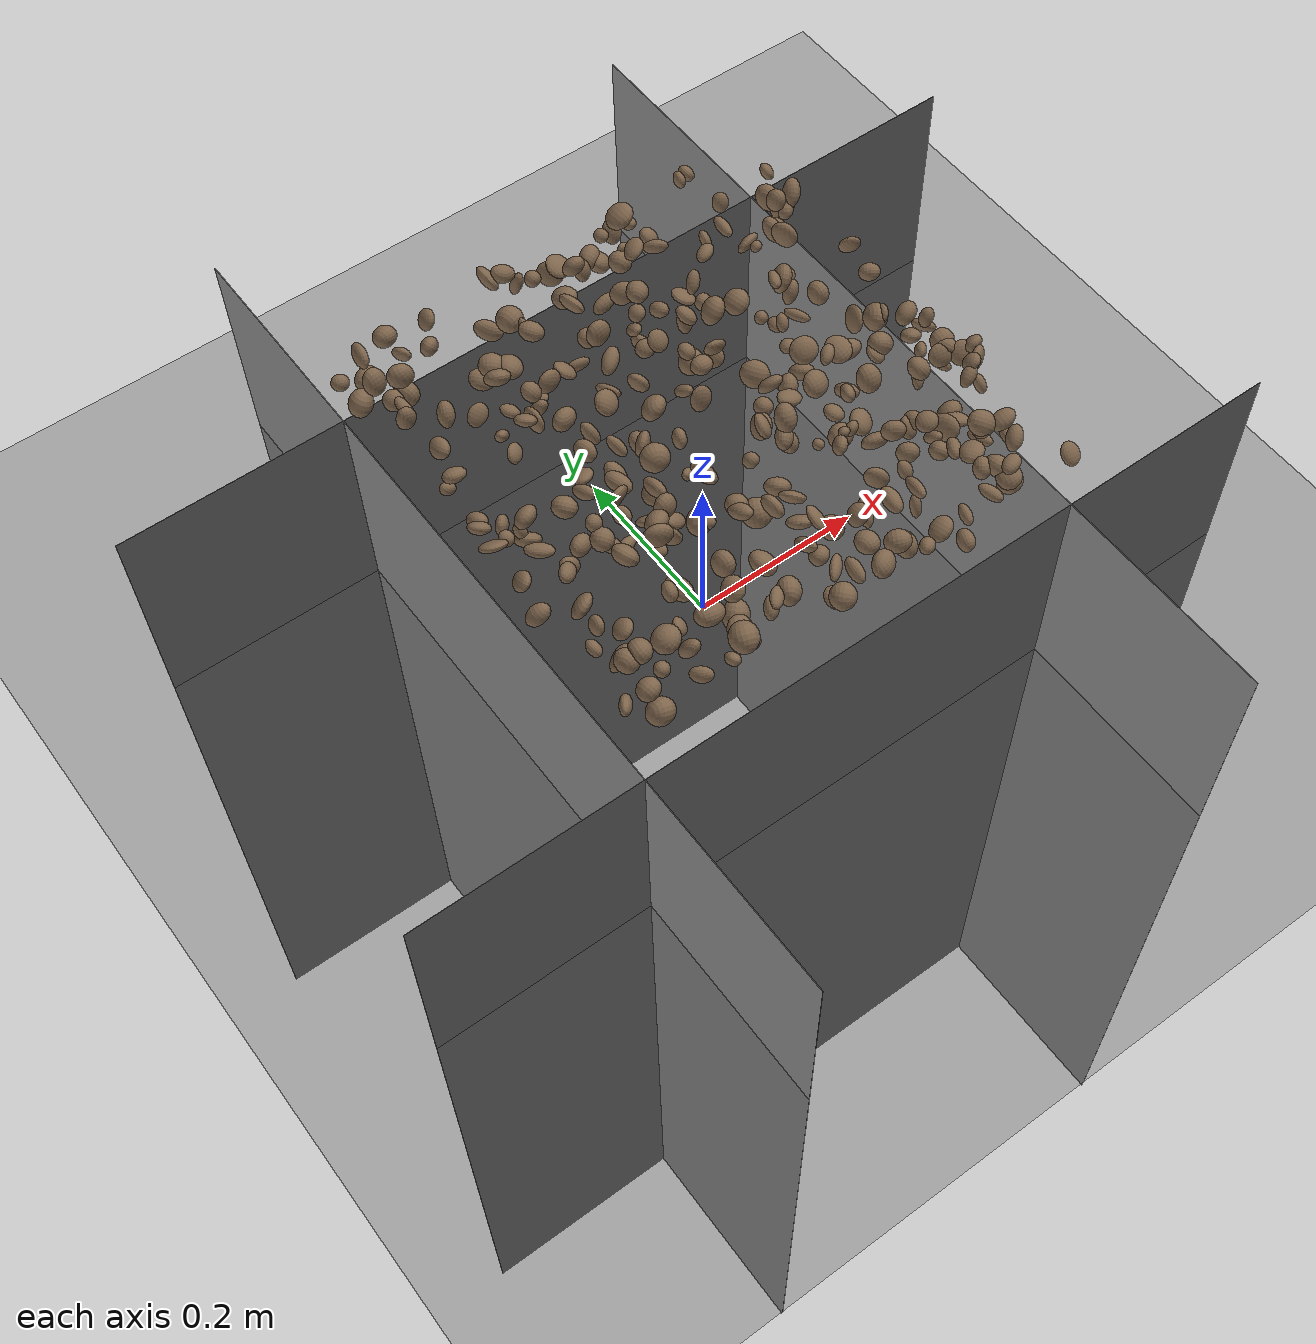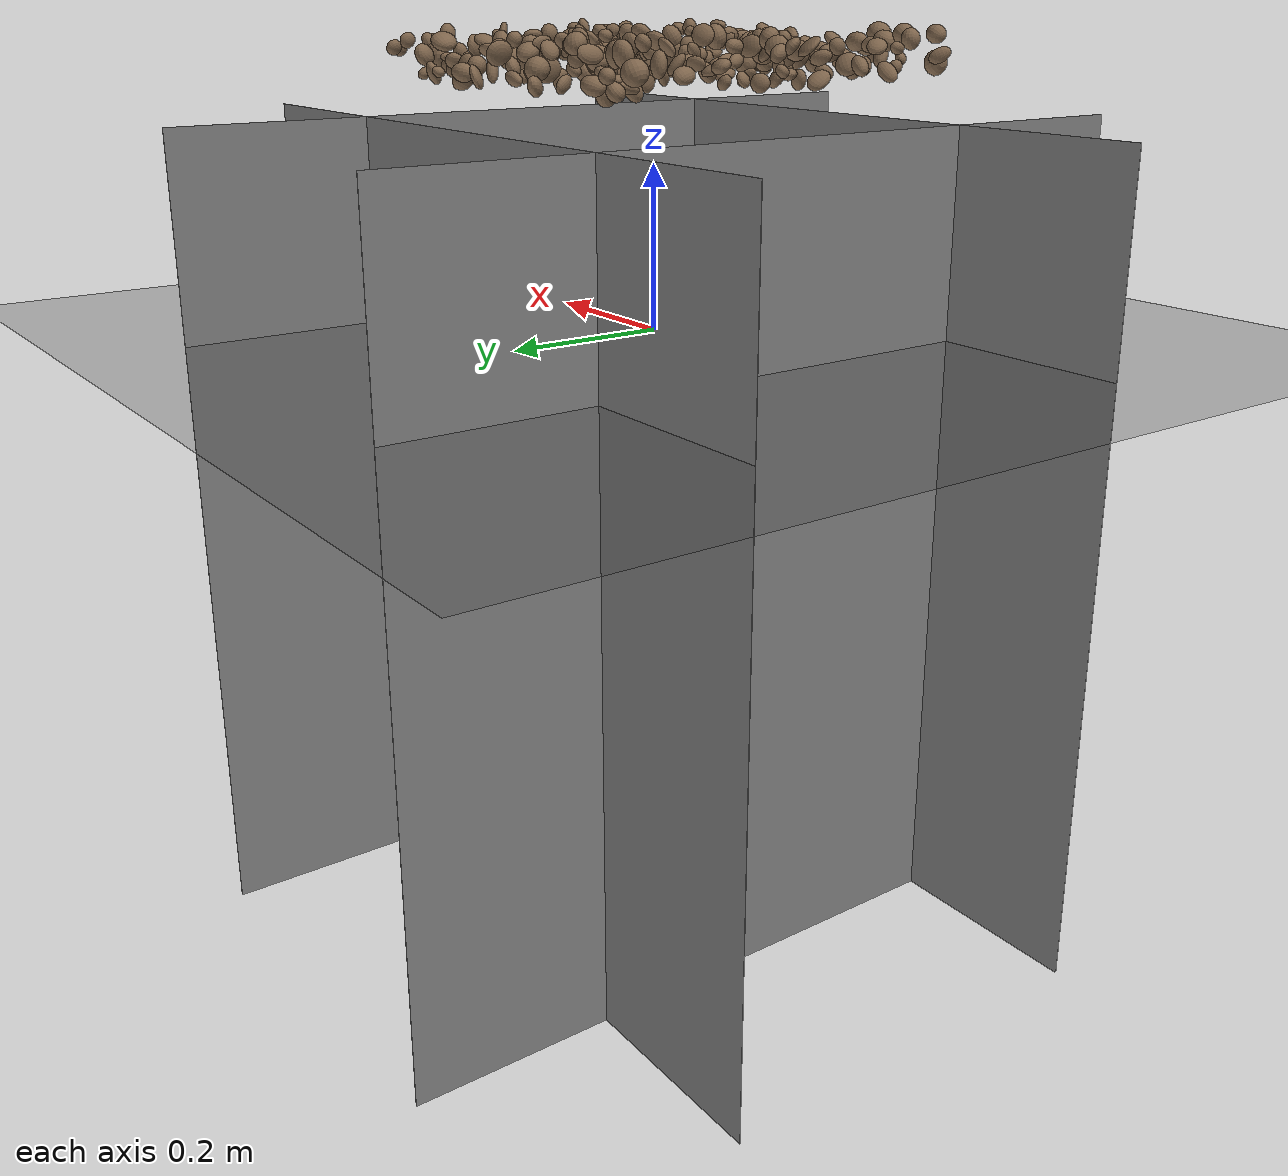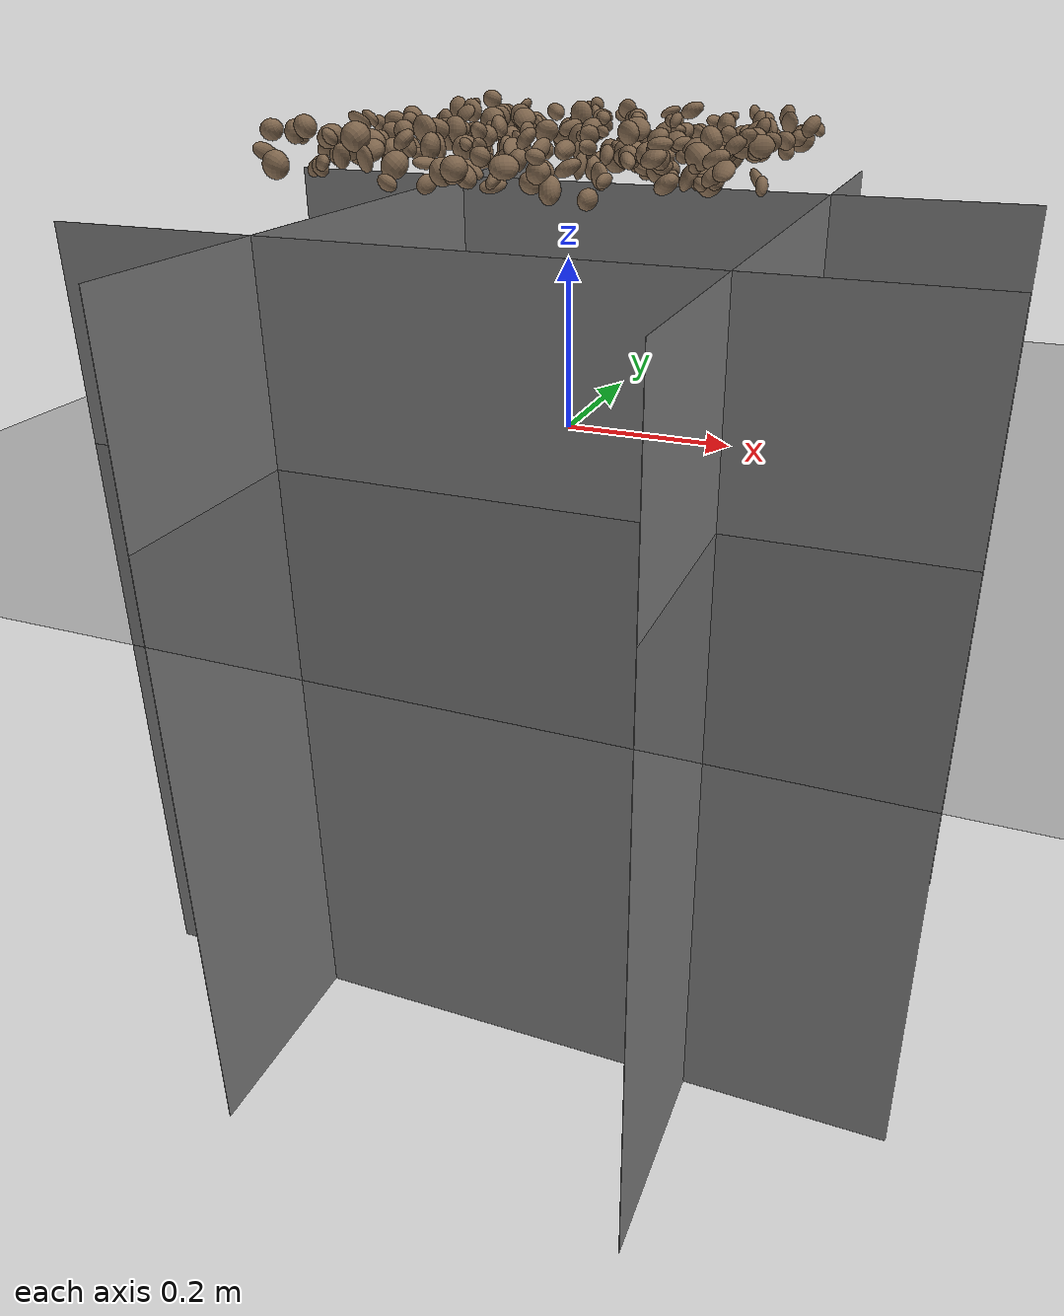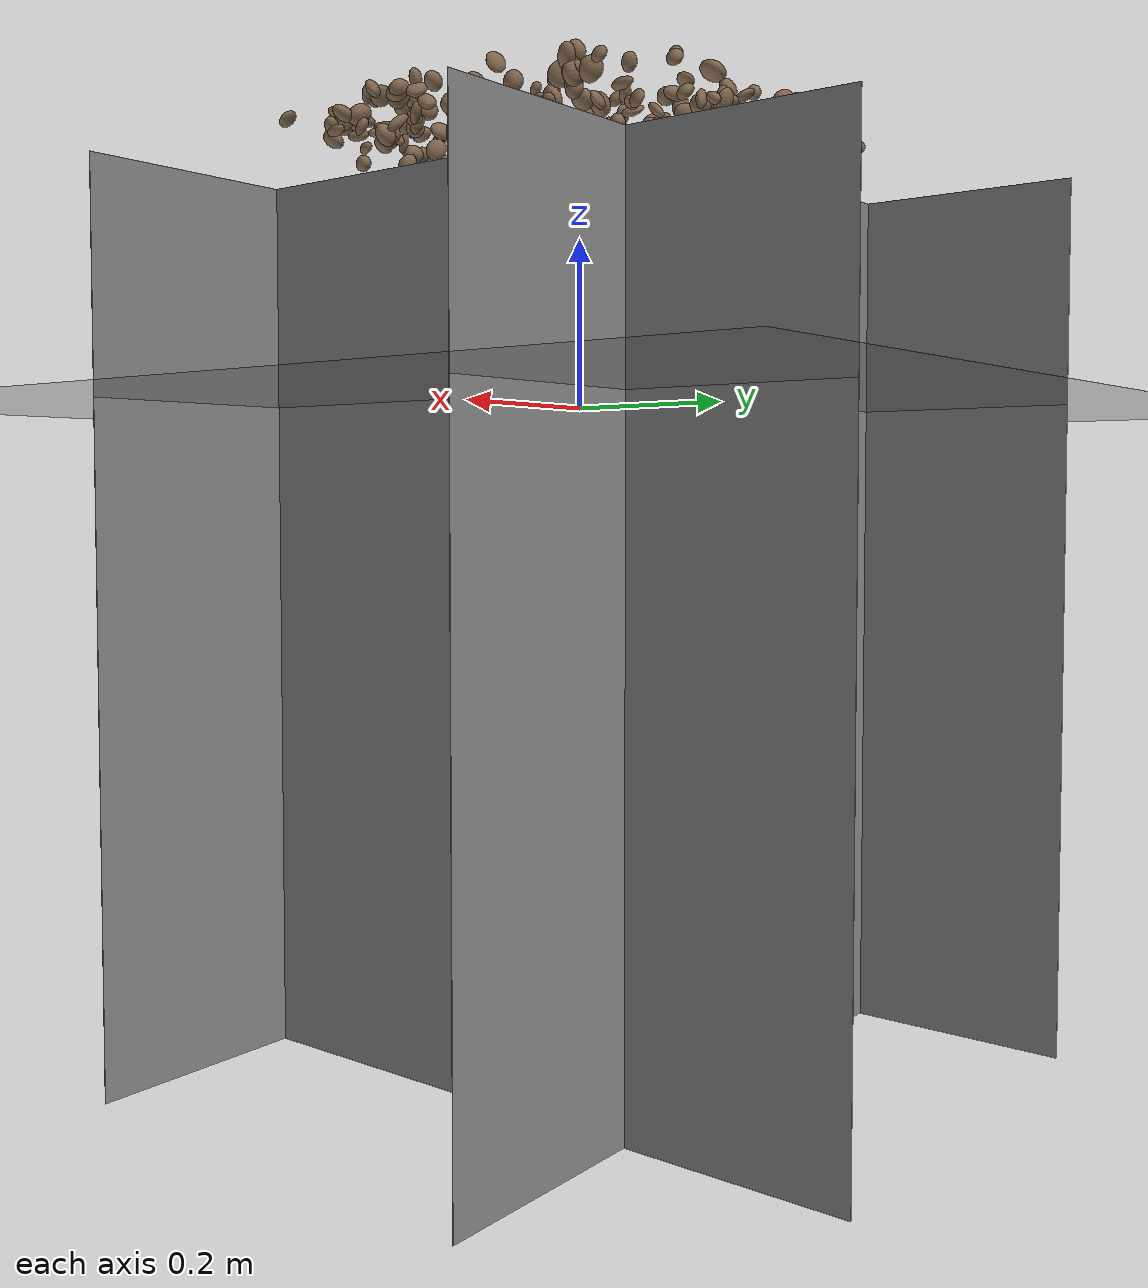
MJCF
<mujoco model="rocky_terrain_scene">

  <default>
    <default class="wall">
      <geom type="plane" size=".5 .5 .05" />
    </default>
  </default>

    <compiler angle="radian" inertiafromgeom="true" />
    <option timestep="0.002" gravity="0 0 -9.81" />

    <worldbody>

        <geom name="+x" class="wall" zaxis="1 0 0" pos="-.25 0 -.25" />
        <geom name="-x" class="wall" zaxis="-1 0 0" pos=".25 0 -.25" />
        <geom name="+y" class="wall" zaxis="0 1 0" pos="0 -.25 -.25" />
        <geom name="-y" class="wall" zaxis="0 -1 0" pos="0 .25 -.25" />

        <light name="sunlight" pos="5 5 5" dir="-1 -1 -1" diffuse="1 1 1" specular="0.5 0.5 0.5" ambient="0.5 0.5 0.5" />

        <geom name="ground_plane" type="plane" size="50 50 0.1" rgba="0.3 0.3 0.3 1" />

        <body name="rocky_terrain_body">

        </body>
    <body name="rock1" pos="-0.16619287956685624 0.06604873283374324 0.3227996512212562"><joint type="free" /><geom type="ellipsoid" size="0.010776852700701368 0.009243667238715926 0.005107807396845329" quat="0.4680800552831909 0.2688125090543739 0.09204229359668925 0.17106514206574588" rgba="0.5 0.4 0.3 1" /><inertial pos="-0.16619287956685624 0.06604873283374324 0.3227996512212562" quat="0.4680800552831909 0.2688125090543739 0.09204229359668925 0.17106514206574588" mass="1.514624359982764e-05" /></body><body name="rock2" pos="0.11438645526364022 0.017305640489706398 0.32284212166427584"><joint type="free" /><geom type="ellipsoid" size="0.008254979515129263 0.007942828897603262 0.006339179201848249" quat="0.016644563451479202 0.8429212787709182 0.1108769741937061 0.02955718358389657" rgba="0.5 0.4 0.3 1" /><inertial pos="0.11438645526364022 0.017305640489706398 0.32284212166427584" quat="0.016644563451479202 0.8429212787709182 0.1108769741937061 0.02955718358389657" mass="5.783310563745762e-05" /></body><body name="rock3" pos="-0.21146095749560362 -0.00933189105498955 0.321264046672334"><joint type="free" /><geom type="ellipsoid" size="0.0059633478420658146 0.011414277920493765 0.0062119464758277195" quat="0.42764985117867305 0.3436658471881584 0.08489854295676198 0.14378575867640656" rgba="0.5 0.4 0.3 1" /><inertial pos="-0.21146095749560362 -0.00933189105498955 0.321264046672334" quat="0.42764985117867305 0.3436658471881584 0.08489854295676198 0.14378575867640656" mass="1.0312993701944355e-05" /></body><body name="rock4" pos="-0.16377153613791107 0.2120318118144282 0.3341275776207498"><joint type="free" /><geom type="ellipsoid" size="0.012515016743076863 0.008220482549652845 0.009961906983593812" quat="0.49305829594537054 0.010376575444619514 0.291050337036179 0.20551479157383096" rgba="0.5 0.4 0.3 1" /><inertial pos="-0.16377153613791107 0.2120318118144282 0.3341275776207498" quat="0.49305829594537054 0.010376575444619514 0.291050337036179 0.20551479157383096" mass="8.694057380186414e-05" /></body><body name="rock5" pos="-0.22390012945086019 -0.004475646899832597 0.3155164639767053"><joint type="free" /><geom type="ellipsoid" size="0.007960252921502176 0.0065107865087744585 0.0076366451267900655" quat="0.2042167158306669 0.32745424555419783 0.11224815591191248 0.3560808827032228" rgba="0.5 0.4 0.3 1" /><inertial pos="-0.22390012945086019 -0.004475646899832597 0.3155164639767053" quat="0.2042167158306669 0.32745424555419783 0.11224815591191248 0.3560808827032228" mass="8.051425501362424e-05" /></body><body name="rock6" pos="0.01032170720925718 0.10515968122993613 0.3101591307409942"><joint type="free" /><geom type="ellipsoid" size="0.007613247302138861 0.009267753806750397 0.010452787718111502" quat="0.4480055745076676 0.16890922549883838 0.3041335959585806 0.07895160403491337" rgba="0.5 0.4 0.3 1" /><inertial pos="0.01032170720925718 0.10515968122993613 0.3101591307409942" quat="0.4480055745076676 0.16890922549883838 0.3041335959585806 0.07895160403491337" mass="6.577357343055519e-05" /></body><body name="rock7" pos="0.14661230813659365 -0.14614352622618793 0.34726285658481065"><joint type="free" /><geom type="ellipsoid" size="0.010332474876565603 0.007286073821977195 0.010958103267680295" quat="0.2755805979130939 0.2791646838217326 0.1274678315914188 0.31778688667375476" rgba="0.5 0.4 0.3 1" /><inertial pos="0.14661230813659365 -0.14614352622618793 0.34726285658481065" quat="0.2755805979130939 0.2791646838217326 0.1274678315914188 0.31778688667375476" mass="4.343009215775886e-05" /></body><body name="rock8" pos="0.18065459546392304 -0.22798839990710879 0.316441811231202"><joint type="free" /><geom type="ellipsoid" size="0.011884312089261006 0.008179149319563837 0.012945904116871031" quat="0.4085929914471929 0.2708978863665937 0.06755221382021996 0.2529569083659935" rgba="0.5 0.4 0.3 1" /><inertial pos="0.18065459546392304 -0.22798839990710879 0.316441811231202" quat="0.4085929914471929 0.2708978863665937 0.06755221382021996 0.2529569083659935" mass="7.806102624818059e-05" /></body><body name="rock9" pos="-0.21233831680499848 0.18544332272737596 0.3049794604159055"><joint type="free" /><geom type="ellipsoid" size="0.014442566016382996 0.005704364227710598 0.006426218116462448" quat="0.16887056485871293 0.30537930883477454 0.27653917326624033 0.2492109530402723" rgba="0.5 0.4 0.3 1" /><inertial pos="-0.21233831680499848 0.18544332272737596 0.3049794604159055" quat="0.16887056485871293 0.30537930883477454 0.27653917326624033 0.2492109530402723" mass="7.797350612914888e-05" /></body><body name="rock10" pos="0.09548735586090279 -0.008563326267464144 0.3018632061032324"><joint type="free" /><geom type="ellipsoid" size="0.012943412563758 0.01076452612626707 0.009125861529228466" quat="0.2292360809083185 0.4341892563483703 0.049334143602804865 0.2872405191405063" rgba="0.5 0.4 0.3 1" /><inertial pos="0.09548735586090279 -0.008563326267464144 0.3018632061032324" quat="0.2292360809083185 0.4341892563483703 0.049334143602804865 0.2872405191405063" mass="7.071078421665946e-05" /></body><body name="rock11" pos="-0.24409757012328037 -0.21707255209594983 0.32683568937358076"><joint type="free" /><geom type="ellipsoid" size="0.005961741347290019 0.008462184443200238 0.01319065158516394" quat="0.10633696200665423 0.14117260838622894 0.4632194361699068 0.28927099343721" rgba="0.5 0.4 0.3 1" /><inertial pos="-0.24409757012328037 -0.21707255209594983 0.32683568937358076" quat="0.10633696200665423 0.14117260838622894 0.4632194361699068 0.28927099343721" mass="6.000564737033711e-05" /></body><body name="rock12" pos="-0.2326322594384515 0.07978796829122548 0.30745839402358194"><joint type="free" /><geom type="ellipsoid" size="0.006384265595699759 0.009363402017507197 0.006967408583492285" quat="0.3530826803230239 0.1934583086517222 0.0858285531528117 0.3676304578724422" rgba="0.5 0.4 0.3 1" /><inertial pos="-0.2326322594384515 0.07978796829122548 0.30745839402358194" quat="0.3530826803230239 0.1934583086517222 0.0858285531528117 0.3676304578724422" mass="5.196058768859141e-05" /></body><body name="rock13" pos="0.22582575747822897 -0.11637636850373995 0.34687926944105907"><joint type="free" /><geom type="ellipsoid" size="0.00953431458440876 0.010647477219443209 0.006223703659106675" quat="0.19884748400787375 0.5597209948825603 0.0808455265009447 0.16058599460862127" rgba="0.5 0.4 0.3 1" /><inertial pos="0.22582575747822897 -0.11637636850373995 0.34687926944105907" quat="0.19884748400787375 0.5597209948825603 0.0808455265009447 0.16058599460862127" mass="9.513115436119778e-05" /></body><body name="rock14" pos="0.14206723625349682 0.18560821925526005 0.3074611523123181"><joint type="free" /><geom type="ellipsoid" size="0.010309606983467647 0.009817923611421253 0.005169661049864651" quat="0.2015249618855699 0.3372326310038225 0.06953074707833787 0.3917116600322697" rgba="0.5 0.4 0.3 1" /><inertial pos="0.14206723625349682 0.18560821925526005 0.3074611523123181" quat="0.2015249618855699 0.3372326310038225 0.06953074707833787 0.3917116600322697" mass="2.4951743038914975e-05" /></body><body name="rock15" pos="-0.2234826225024062 0.23419781289469171 0.3095999728518814"><joint type="free" /><geom type="ellipsoid" size="0.011282720433543714 0.009872469127471254 0.013334888443830305" quat="0.28018140647244394 0.1123351642552103 0.2961365846187949 0.31134684465355095" rgba="0.5 0.4 0.3 1" /><inertial pos="-0.2234826225024062 0.23419781289469171 0.3095999728518814" quat="0.28018140647244394 0.1123351642552103 0.2961365846187949 0.31134684465355095" mass="3.106539648914779e-05" /></body><body name="rock16" pos="0.07350548986464617 0.23464705268474995 0.34191933252963763"><joint type="free" /><geom type="ellipsoid" size="0.014547423698542155 0.008756433735035887 0.01484954364198058" quat="0.32695265883441205 0.1704280603410396 0.2088203531918951 0.29379892763265325" rgba="0.5 0.4 0.3 1" /><inertial pos="0.07350548986464617 0.23464705268474995 0.34191933252963763" quat="0.32695265883441205 0.1704280603410396 0.2088203531918951 0.29379892763265325" mass="3.5022340616844576e-05" /></body><body name="rock17" pos="-0.05445198318319727 -0.2008712381038314 0.3136677473499343"><joint type="free" /><geom type="ellipsoid" size="0.011691768451680584 0.01391899269876469 0.013708375310761373" quat="0.14113887375137124 0.09238802212413755 0.3800175971696989 0.3864555069547922" rgba="0.5 0.4 0.3 1" /><inertial pos="-0.05445198318319727 -0.2008712381038314 0.3136677473499343" quat="0.14113887375137124 0.09238802212413755 0.3800175971696989 0.3864555069547922" mass="1.3498786552697e-05" /></body><body name="rock18" pos="-0.1481203417165579 -0.14995431622399163 0.3346835060642099"><joint type="free" /><geom type="ellipsoid" size="0.01016294887558206 0.00983168708486384 0.007320669212899918" quat="0.18545141262494588 0.37135672439759676 0.060891708122637826 0.38230015485481955" rgba="0.5 0.4 0.3 1" /><inertial pos="-0.1481203417165579 -0.14995431622399163 0.3346835060642099" quat="0.18545141262494588 0.37135672439759676 0.060891708122637826 0.38230015485481955" mass="3.3702393104576895e-05" /></body><body name="rock19" pos="0.2336304102722762 0.16505741752532777 0.33365157052707994"><joint type="free" /><geom type="ellipsoid" size="0.009589001510013798 0.014753664348098182 0.00861051838198882" quat="0.28546844302427754 0.2550745642564377 0.3735616670482292 0.08589532567105546" rgba="0.5 0.4 0.3 1" /><inertial pos="0.2336304102722762 0.16505741752532777 0.33365157052707994" quat="0.28546844302427754 0.2550745642564377 0.3735616670482292 0.08589532567105546" mass="8.451817699159535e-05" /></body><body name="rock20" pos="0.22536473881387092 -0.05096692891141674 0.34958492090413157"><joint type="free" /><geom type="ellipsoid" size="0.006964281876063733 0.010710259506547411 0.006498915864631548" quat="0.10006045202640679 0.21793365665723535 0.38954297433951374 0.2924629169768441" rgba="0.5 0.4 0.3 1" /><inertial pos="0.22536473881387092 -0.05096692891141674 0.34958492090413157" quat="0.10006045202640679 0.21793365665723535 0.38954297433951374 0.2924629169768441" mass="3.9676463279974304e-05" /></body><body name="rock21" pos="-0.17529763246373675 0.11054159231991023 0.3408948269230555"><joint type="free" /><geom type="ellipsoid" size="0.005307480609369243 0.009876127689496018 0.012047927605642907" quat="0.4023388632692552 0.06804676635771337 0.2492602643132961 0.2803541060597353" rgba="0.5 0.4 0.3 1" /><inertial pos="-0.17529763246373675 0.11054159231991023 0.3408948269230555" quat="0.4023388632692552 0.06804676635771337 0.2492602643132961 0.2803541060597353" mass="1.9003209824572357e-05" /></body><body name="rock22" pos="-0.20614653424762341 0.19530537022870104 0.3372108193088671"><joint type="free" /><geom type="ellipsoid" size="0.009746063868331009 0.014242998552013313 0.013103454859878877" quat="0.32767023225770364 0.22539520564981966 0.17314907866702914 0.27378548342544756" rgba="0.5 0.4 0.3 1" /><inertial pos="-0.20614653424762341 0.19530537022870104 0.3372108193088671" quat="0.32767023225770364 0.22539520564981966 0.17314907866702914 0.27378548342544756" mass="7.592102707624936e-05" /></body><body name="rock23" pos="-0.07769816640676813 -0.09928267532620433 0.3257540483170638"><joint type="free" /><geom type="ellipsoid" size="0.012774731227849879 0.011818950597232447 0.013737229494755285" quat="0.3050123093740004 0.023243878160517494 0.35094828384283405 0.320795528622648" rgba="0.5 0.4 0.3 1" /><inertial pos="-0.07769816640676813 -0.09928267532620433 0.3257540483170638" quat="0.3050123093740004 0.023243878160517494 0.35094828384283405 0.320795528622648" mass="4.723034111470708e-05" /></body><body name="rock24" pos="-0.1653103420013572 -0.2021562059288809 0.3240400168830167"><joint type="free" /><geom type="ellipsoid" size="0.0076504493612336395 0.01468165467336146 0.00857860041502805" quat="0.09188968408169254 0.2802188976319862 0.2625453576003204 0.36534606068600073" rgba="0.5 0.4 0.3 1" /><inertial pos="-0.1653103420013572 -0.2021562059288809 0.3240400168830167" quat="0.09188968408169254 0.2802188976319862 0.2625453576003204 0.36534606068600073" mass="5.619342352561629e-05" /></body><body name="rock25" pos="-0.0711270373736212 -0.20432586017986837 0.32178579954610115"><joint type="free" /><geom type="ellipsoid" size="0.0071280425465374995 0.005165728563216636 0.012655680239635727" quat="0.021963081071261086 0.2763298483259947 0.31300438783688767 0.38870268276585646" rgba="0.5 0.4 0.3 1" /><inertial pos="-0.0711270373736212 -0.20432586017986837 0.32178579954610115" quat="0.021963081071261086 0.2763298483259947 0.31300438783688767 0.38870268276585646" mass="2.647024084872597e-05" /></body><body name="rock26" pos="-0.06048685810735577 0.06523824081875146 0.3366937806004437"><joint type="free" /><geom type="ellipsoid" size="0.013973468938853043 0.005031885515267337 0.00863654606500858" quat="0.12889299731972173 0.320811302616825 0.5030298752084846 0.04726582485496855" rgba="0.5 0.4 0.3 1" /><inertial pos="-0.06048685810735577 0.06523824081875146 0.3366937806004437" quat="0.12889299731972173 0.320811302616825 0.5030298752084846 0.04726582485496855" mass="5.312792583739986e-05" /></body><body name="rock27" pos="-0.13662291310301594 -0.1480703279304823 0.3269996790342691"><joint type="free" /><geom type="ellipsoid" size="0.014885532033503172 0.010365943966063594 0.010298651265459525" quat="0.26582806514079826 0.1710091252932036 0.19543595545547374 0.3677268541105243" rgba="0.5 0.4 0.3 1" /><inertial pos="-0.13662291310301594 -0.1480703279304823 0.3269996790342691" quat="0.26582806514079826 0.1710091252932036 0.19543595545547374 0.3677268541105243" mass="6.556267870898895e-05" /></body><body name="rock28" pos="-0.22668795561203747 -0.22729144732847822 0.3488645379005294"><joint type="free" /><geom type="ellipsoid" size="0.011086141769372854 0.010189809858615985 0.01163694586037051" quat="0.3669894774842229 0.11979499509473227 0.2756254245657807 0.2375901028552641" rgba="0.5 0.4 0.3 1" /><inertial pos="-0.22668795561203747 -0.22729144732847822 0.3488645379005294" quat="0.3669894774842229 0.11979499509473227 0.2756254245657807 0.2375901028552641" mass="6.04327510847025e-05" /></body><body name="rock29" pos="-0.2358170920227215 -0.04536672953715548 0.30546317797881284"><joint type="free" /><geom type="ellipsoid" size="0.014614175862907534 0.0062356985993194235 0.01035348575268331" quat="0.4073435782482392 0.06323694393535977 0.2528694578374612 0.27655001997893985" rgba="0.5 0.4 0.3 1" /><inertial pos="-0.2358170920227215 -0.04536672953715548 0.30546317797881284" quat="0.4073435782482392 0.06323694393535977 0.2528694578374612 0.27655001997893985" mass="3.375256965783807e-05" /></body><body name="rock30" pos="-0.13569636203257102 -0.1914250060978412 0.3386000925040448"><joint type="free" /><geom type="ellipsoid" size="0.011496850779215027 0.01105764977341763 0.014932616465995599" quat="0.2186359844139168 0.31037331081241937 0.22798281138743268 0.24300789338623108" rgba="0.5 0.4 0.3 1" /><inertial pos="-0.13569636203257102 -0.1914250060978412 0.3386000925040448" quat="0.2186359844139168 0.31037331081241937 0.22798281138743268 0.24300789338623108" mass="1.992828086370262e-05" /></body><body name="rock31" pos="0.2162372703617803 -0.03281883677447789 0.3450794615398973"><joint type="free" /><geom type="ellipsoid" size="0.009455956355117406 0.01260474413420451 0.009413524791539535" quat="0.12088484453419567 0.3394234459460977 0.44449999454613337 0.0951917149735732" rgba="0.5 0.4 0.3 1" /><inertial pos="0.2162372703617803 -0.03281883677447789 0.3450794615398973" quat="0.12088484453419567 0.3394234459460977 0.44449999454613337 0.0951917149735732" mass="4.6083837079086194e-05" /></body><body name="rock32" pos="0.2091064057452594 0.15602349222795553 0.3076801353270731"><joint type="free" /><geom type="ellipsoid" size="0.009487399771668216 0.010621143493617485 0.008335049956749377" quat="0.5421629168168343 0.3055641098155507 0.009985779410826795 0.14228719395678818" rgba="0.5 0.4 0.3 1" /><inertial pos="0.2091064057452594 0.15602349222795553 0.3076801353270731" quat="0.5421629168168343 0.3055641098155507 0.009985779410826795 0.14228719395678818" mass="1.6388369903998687e-05" /></body><body name="rock33" pos="0.18567817264565084 0.005658994697279762 0.3231434836936992"><joint type="free" /><geom type="ellipsoid" size="0.012336301735612672 0.014066571583395089 0.005277724863104082" quat="0.27869165240097393 0.2239873897690767 0.3848623446916998 0.11245861313824962" rgba="0.5 0.4 0.3 1" /><inertial pos="0.18567817264565084 0.005658994697279762 0.3231434836936992" quat="0.27869165240097393 0.2239873897690767 0.3848623446916998 0.11245861313824962" mass="6.80979243560575e-05" /></body><body name="rock34" pos="-0.1383086610617692 0.1642177268240253 0.31385897580697936"><joint type="free" /><geom type="ellipsoid" size="0.01295351329639792 0.007415846755690854 0.010667336877269347" quat="0.13255301721769133 0.1664174553831532 0.22699507608472208 0.4740344513144334" rgba="0.5 0.4 0.3 1" /><inertial pos="-0.1383086610617692 0.1642177268240253 0.31385897580697936" quat="0.13255301721769133 0.1664174553831532 0.22699507608472208 0.4740344513144334" mass="2.1232610307451687e-05" /></body><body name="rock35" pos="-0.0704279492445673 0.1885106261258519 0.31570299599930046"><joint type="free" /><geom type="ellipsoid" size="0.013061873249104052 0.014662930522128564 0.005650534177099626" quat="0.1793514565019131 0.3282215710012016 0.10200751066549049 0.39041946183139475" rgba="0.5 0.4 0.3 1" /><inertial pos="-0.0704279492445673 0.1885106261258519 0.31570299599930046" quat="0.1793514565019131 0.3282215710012016 0.10200751066549049 0.39041946183139475" mass="3.552418519156502e-05" /></body><body name="rock36" pos="0.09406579256020114 0.24884723147027116 0.307708146441533"><joint type="free" /><geom type="ellipsoid" size="0.006260774102896532 0.008657334527905588 0.007223283002735243" quat="0.11729430224162343 0.38486512089592606 0.0965162355587446 0.401324341303706" rgba="0.5 0.4 0.3 1" /><inertial pos="0.09406579256020114 0.24884723147027116 0.307708146441533" quat="0.11729430224162343 0.38486512089592606 0.0965162355587446 0.401324341303706" mass="8.231181687765397e-05" /></body><body name="rock37" pos="0.20744645329776457 0.15679774598038848 0.3454273631716047"><joint type="free" /><geom type="ellipsoid" size="0.010004051544889009 0.01216801227604163 0.008599295059021827" quat="0.17399287481637896 0.270045754868244 0.28584680896364345 0.2701145613517336" rgba="0.5 0.4 0.3 1" /><inertial pos="0.20744645329776457 0.15679774598038848 0.3454273631716047" quat="0.17399287481637896 0.270045754868244 0.28584680896364345 0.2701145613517336" mass="4.322880963048725e-05" /></body><body name="rock38" pos="0.1698127053098223 -0.2205739523153401 0.33956576735135946"><joint type="free" /><geom type="ellipsoid" size="0.01390959448400577 0.013064942830977953 0.009959069434452605" quat="0.2195419614980679 0.19423490150104258 0.1877515023546232 0.3984716346462663" rgba="0.5 0.4 0.3 1" /><inertial pos="0.1698127053098223 -0.2205739523153401 0.33956576735135946" quat="0.2195419614980679 0.19423490150104258 0.1877515023546232 0.3984716346462663" mass="8.37517675478477e-05" /></body><body name="rock39" pos="-0.11505240413350121 -0.027097311512316424 0.3364682040468774"><joint type="free" /><geom type="ellipsoid" size="0.014589674840631 0.008835460127370149 0.008841216227627338" quat="0.2376707175094477 0.17708554581080685 0.21128127567045518 0.37396246100929026" rgba="0.5 0.4 0.3 1" /><inertial pos="-0.11505240413350121 -0.027097311512316424 0.3364682040468774" quat="0.2376707175094477 0.17708554581080685 0.21128127567045518 0.37396246100929026" mass="9.58252692209422e-05" /></body><body name="rock40" pos="-0.07692024925665997 0.20706583820649488 0.31833964040760054"><joint type="free" /><geom type="ellipsoid" size="0.013143998649548586 0.014222372514585396 0.01340105911835733" quat="0.012541392138939489 0.3987130638717259 0.14226229317452083 0.4464832508148138" rgba="0.5 0.4 0.3 1" /><inertial pos="-0.07692024925665997 0.20706583820649488 0.31833964040760054" quat="0.012541392138939489 0.3987130638717259 0.14226229317452083 0.4464832508148138" mass="2.2066735068592917e-05" /></body><body name="rock41" pos="-0.04063517645582254 -0.018956234700271524 0.3355410167406657"><joint type="free" /><geom type="ellipsoid" size="0.009842958677662848 0.010373505653192032 0.006693616595291224" quat="0.2949241883158501 0.2831146197206328 0.24071755703331704 0.1812436349302001" rgba="0.5 0.4 0.3 1" /><inertial pos="-0.04063517645582254 -0.018956234700271524 0.3355410167406657" quat="0.2949241883158501 0.2831146197206328 0.24071755703331704 0.1812436349302001" mass="7.11923142709099e-05" /></body><body name="rock42" pos="-0.08436378694388408 -0.03996136557252822 0.3181857251542346"><joint type="free" /><geom type="ellipsoid" size="0.01478901527624732 0.009300286886355213 0.006907813793168368" quat="0.26176652868938854 0.21201562441702523 0.29336361871671934 0.2328542281768669" rgba="0.5 0.4 0.3 1" /><inertial pos="-0.08436378694388408 -0.03996136557252822 0.3181857251542346" quat="0.26176652868938854 0.21201562441702523 0.29336361871671934 0.2328542281768669" mass="4.420146315860536e-05" /></body><body name="rock43" pos="0.2160517532724136 -0.08637793334531418 0.33607631080747224"><joint type="free" /><geom type="ellipsoid" size="0.01225839310644362 0.006568727119650182 0.013427266272083814" quat="0.14758990570412506 0.39175277590983315 0.05931361010162277 0.40134370828441895" rgba="0.5 0.4 0.3 1" /><inertial pos="0.2160517532724136 -0.08637793334531418 0.33607631080747224" quat="0.14758990570412506 0.39175277590983315 0.05931361010162277 0.40134370828441895" mass="8.243708745371483e-05" /></body><body name="rock44" pos="-0.05061006004124324 -0.06998446209329295 0.3448297329686736"><joint type="free" /><geom type="ellipsoid" size="0.014549745745259319 0.00792875205276336 0.010847378886805393" quat="0.021615236462323092 0.36635002654128357 0.4904006188987638 0.12163411809762957" rgba="0.5 0.4 0.3 1" /><inertial pos="-0.05061006004124324 -0.06998446209329295 0.3448297329686736" quat="0.021615236462323092 0.36635002654128357 0.4904006188987638 0.12163411809762957" mass="3.535779953829265e-05" /></body><body name="rock45" pos="-0.10938779970104923 -0.09460486039476179 0.32476129018382893"><joint type="free" /><geom type="ellipsoid" size="0.013571228066824037 0.013969382820224842 0.005346083876513297" quat="0.2527473320015447 0.06933040917399484 0.3633731551452562 0.3145491036792043" rgba="0.5 0.4 0.3 1" /><inertial pos="-0.10938779970104923 -0.09460486039476179 0.32476129018382893" quat="0.2527473320015447 0.06933040917399484 0.3633731551452562 0.3145491036792043" mass="7.76292321540014e-05" /></body><body name="rock46" pos="0.015283629528264231 0.1194609474276514 0.3006404544189016"><joint type="free" /><geom type="ellipsoid" size="0.011711511204288691 0.006412646785403892 0.011544959600314597" quat="0.022635719085535737 0.39436960317150954 0.5279572110871333 0.05503746665582137" rgba="0.5 0.4 0.3 1" /><inertial pos="0.015283629528264231 0.1194609474276514 0.3006404544189016" quat="0.022635719085535737 0.39436960317150954 0.5279572110871333 0.05503746665582137" mass="5.0350515937677175e-05" /></body><body name="rock47" pos="-0.060405946397847965 -0.05926509906253985 0.33973219330666077"><joint type="free" /><geom type="ellipsoid" size="0.005234323169054589 0.006298071795221759 0.01182198327888723" quat="0.0993888087169434 0.26221651253496403 0.44688576900324356 0.1915089097448491" rgba="0.5 0.4 0.3 1" /><inertial pos="-0.060405946397847965 -0.05926509906253985 0.33973219330666077" quat="0.0993888087169434 0.26221651253496403 0.44688576900324356 0.1915089097448491" mass="5.963041456459686e-05" /></body><body name="rock48" pos="-0.22472783453784034 0.07816855145703372 0.3231530128292181"><joint type="free" /><geom type="ellipsoid" size="0.01026686429969776 0.007127925104878566 0.011874659470794826" quat="0.3168775697468442 0.20478320679155382 0.32118157799850733 0.15715764546309463" rgba="0.5 0.4 0.3 1" /><inertial pos="-0.22472783453784034 0.07816855145703372 0.3231530128292181" quat="0.3168775697468442 0.20478320679155382 0.32118157799850733 0.15715764546309463" mass="3.739325241493826e-05" /></body><body name="rock49" pos="0.09613040828286545 -0.10144788841724883 0.330855866652786"><joint type="free" /><geom type="ellipsoid" size="0.005724406041229908 0.00797471259987283 0.007451137349582981" quat="0.07574729238324934 0.3153959279545757 0.42835435460772375 0.18050242505445113" rgba="0.5 0.4 0.3 1" /><inertial pos="0.09613040828286545 -0.10144788841724883 0.330855866652786" quat="0.07574729238324934 0.3153959279545757 0.42835435460772375 0.18050242505445113" mass="2.3255003681276353e-05" /></body><body name="rock50" pos="-0.10022589984839364 0.10408235014109951 0.3410946327923702"><joint type="free" /><geom type="ellipsoid" size="0.0065439187135142365 0.012779313714775076 0.012689442534615708" quat="0.17035117952403012 0.30143564979359216 0.35670912750059386 0.17150404318178378" rgba="0.5 0.4 0.3 1" /><inertial pos="-0.10022589984839364 0.10408235014109951 0.3410946327923702" quat="0.17035117952403012 0.30143564979359216 0.35670912750059386 0.17150404318178378" mass="2.3497907177410776e-05" /></body><body name="rock51" pos="-0.12180489728107396 -0.21720832580239696 0.33254608857717427"><joint type="free" /><geom type="ellipsoid" size="0.013499629778217944 0.009500749509014084 0.012122592750998884" quat="0.21463881215455835 0.4180133152353671 0.14054548439240902 0.2268023882176655" rgba="0.5 0.4 0.3 1" /><inertial pos="-0.12180489728107396 -0.21720832580239696 0.33254608857717427" quat="0.21463881215455835 0.4180133152353671 0.14054548439240902 0.2268023882176655" mass="6.406329313927884e-05" /></body><body name="rock52" pos="0.060700947537935035 0.2498065516846112 0.3106622351935424"><joint type="free" /><geom type="ellipsoid" size="0.007334456145296583 0.005853912064931505 0.007644687103600138" quat="0.34395036721983824 0.3965963415865379 0.029156723100285078 0.23029656809333882" rgba="0.5 0.4 0.3 1" /><inertial pos="0.060700947537935035 0.2498065516846112 0.3106622351935424" quat="0.34395036721983824 0.3965963415865379 0.029156723100285078 0.23029656809333882" mass="2.4543297382638966e-05" /></body><body name="rock53" pos="-0.0012889953074450844 0.20594823353726927 0.34384028571464625"><joint type="free" /><geom type="ellipsoid" size="0.01257386308682764 0.008236023138503072 0.010467430183727845" quat="0.2884365510660399 0.05506885909074028 0.5276426349342288 0.12885195490899098" rgba="0.5 0.4 0.3 1" /><inertial pos="-0.0012889953074450844 0.20594823353726927 0.34384028571464625" quat="0.2884365510660399 0.05506885909074028 0.5276426349342288 0.12885195490899098" mass="8.520390494912587e-05" /></body><body name="rock54" pos="-0.21287241128839146 -0.10740823426783874 0.3191360199591622"><joint type="free" /><geom type="ellipsoid" size="0.007043635765280614 0.013878644618171381 0.01357836602364643" quat="0.23896936580457515 0.2008192593803596 0.03656433503989226 0.5236470397751731" rgba="0.5 0.4 0.3 1" /><inertial pos="-0.21287241128839146 -0.10740823426783874 0.3191360199591622" quat="0.23896936580457515 0.2008192593803596 0.03656433503989226 0.5236470397751731" mass="5.164477693565459e-05" /></body><body name="rock55" pos="-0.20542655988282166 -0.011190905814802476 0.3402648515997238"><joint type="free" /><geom type="ellipsoid" size="0.00860003814519471 0.012143076859460335 0.012945211493723477" quat="0.06352562466436837 0.2998646952393162 0.31835710105023085 0.3182525790460845" rgba="0.5 0.4 0.3 1" /><inertial pos="-0.20542655988282166 -0.011190905814802476 0.3402648515997238" quat="0.06352562466436837 0.2998646952393162 0.31835710105023085 0.3182525790460845" mass="8.971518400779166e-05" /></body><body name="rock56" pos="0.05910409659099097 0.19057792989225708 0.3426574557674218"><joint type="free" /><geom type="ellipsoid" size="0.012590516526839735 0.005560868386525836 0.010124245178206148" quat="0.43995062694019144 0.31478664597207506 0.04330763868681553 0.20195508840091803" rgba="0.5 0.4 0.3 1" /><inertial pos="0.05910409659099097 0.19057792989225708 0.3426574557674218" quat="0.43995062694019144 0.31478664597207506 0.04330763868681553 0.20195508840091803" mass="6.84803887313732e-05" /></body><body name="rock57" pos="0.08933481559470419 -0.1478460337917034 0.30979479291228923"><joint type="free" /><geom type="ellipsoid" size="0.007191072621142841 0.011805246777068318 0.013457697958246244" quat="0.13209436514897088 0.541928281989394 0.2502802730923723 0.07569707976926277" rgba="0.5 0.4 0.3 1" /><inertial pos="0.08933481559470419 -0.1478460337917034 0.30979479291228923" quat="0.13209436514897088 0.541928281989394 0.2502802730923723 0.07569707976926277" mass="4.9277584362688985e-05" /></body><body name="rock58" pos="0.16338204329511652 -0.04641175535702474 0.30136318580358534"><joint type="free" /><geom type="ellipsoid" size="0.014933831584783591 0.010882517169466472 0.012528285275560155" quat="0.12518018257009556 0.4012384758466657 0.06946659937319727 0.4041147422100415" rgba="0.5 0.4 0.3 1" /><inertial pos="0.16338204329511652 -0.04641175535702474 0.30136318580358534" quat="0.12518018257009556 0.4012384758466657 0.06946659937319727 0.4041147422100415" mass="8.956063645122286e-05" /></body><body name="rock59" pos="-0.12207644164578257 -0.23120447259454258 0.32654283529394507"><joint type="free" /><geom type="ellipsoid" size="0.006023666603569232 0.014253273163208145 0.009920584937753265" quat="0.2442776051626494 0.35160412082976483 0.18038267582039796 0.22373559818718772" rgba="0.5 0.4 0.3 1" /><inertial pos="-0.12207644164578257 -0.23120447259454258 0.32654283529394507" quat="0.2442776051626494 0.35160412082976483 0.18038267582039796 0.22373559818718772" mass="1.3935146345230864e-05" /></body><body name="rock60" pos="-0.2498490980427147 0.23585587530351948 0.3200338189546199"><joint type="free" /><geom type="ellipsoid" size="0.008352186313497238 0.008295095607946303 0.00899614231902042" quat="0.2553625363899679 0.342890047957864 0.11672131584207637 0.2850260998100917" rgba="0.5 0.4 0.3 1" /><inertial pos="-0.2498490980427147 0.23585587530351948 0.3200338189546199" quat="0.2553625363899679 0.342890047957864 0.11672131584207637 0.2850260998100917" mass="6.0941692873494105e-05" /></body><body name="rock61" pos="-0.2144003363259358 -0.16629816441560774 0.30922187461241324"><joint type="free" /><geom type="ellipsoid" size="0.006452021348340357 0.009808518730886732 0.014407246269781217" quat="0.1468996361942679 0.2165345241582574 0.1079530467330622 0.5286127929144124" rgba="0.5 0.4 0.3 1" /><inertial pos="-0.2144003363259358 -0.16629816441560774 0.30922187461241324" quat="0.1468996361942679 0.2165345241582574 0.1079530467330622 0.5286127929144124" mass="4.0609767185676244e-05" /></body><body name="rock62" pos="0.11356896573327735 0.026359448598651913 0.3480029926550217"><joint type="free" /><geom type="ellipsoid" size="0.00914067434795092 0.005799832631295476 0.006007527396836729" quat="0.20750929246593697 0.3955913403646732 0.07526585384618165 0.32163351332320816" rgba="0.5 0.4 0.3 1" /><inertial pos="0.11356896573327735 0.026359448598651913 0.3480029926550217" quat="0.20750929246593697 0.3955913403646732 0.07526585384618165 0.32163351332320816" mass="5.259778284382218e-05" /></body><body name="rock63" pos="0.21851558239781366 0.18370178905673357 0.3209875014395301"><joint type="free" /><geom type="ellipsoid" size="0.014034242207404735 0.012619919745935043 0.009615849705603367" quat="0.0439948958846573 0.3887534589841835 0.2318085919234896 0.33544305320766965" rgba="0.5 0.4 0.3 1" /><inertial pos="0.21851558239781366 0.18370178905673357 0.3209875014395301" quat="0.0439948958846573 0.3887534589841835 0.2318085919234896 0.33544305320766965" mass="3.402010526929639e-05" /></body><body name="rock64" pos="0.19510049107901845 0.12658164824077384 0.3305897032523778"><joint type="free" /><geom type="ellipsoid" size="0.0071373680436613435 0.014416802618894487 0.013324932272219977" quat="0.4850976267911416 0.2929808203131348 0.09595893770594999 0.1259626151897736" rgba="0.5 0.4 0.3 1" /><inertial pos="0.19510049107901845 0.12658164824077384 0.3305897032523778" quat="0.4850976267911416 0.2929808203131348 0.09595893770594999 0.1259626151897736" mass="8.55746018851691e-05" /></body><body name="rock65" pos="0.06528734141266407 -0.21943388350486204 0.30485893011231513"><joint type="free" /><geom type="ellipsoid" size="0.010493278867091966 0.014541132749141445 0.010756324008681059" quat="0.3613772761422667 0.1781660556774461 0.2733360143063928 0.18712065387389434" rgba="0.5 0.4 0.3 1" /><inertial pos="0.06528734141266407 -0.21943388350486204 0.30485893011231513" quat="0.3613772761422667 0.1781660556774461 0.2733360143063928 0.18712065387389434" mass="9.350142169381822e-05" /></body><body name="rock66" pos="0.13140942572022823 0.1714361328918091 0.30771769040971736"><joint type="free" /><geom type="ellipsoid" size="0.01193280030685555 0.006457889646542387 0.007867632127927229" quat="0.45375112178125176 0.34765240156614 0.06830965064788103 0.13028682600472719" rgba="0.5 0.4 0.3 1" /><inertial pos="0.13140942572022823 0.1714361328918091 0.30771769040971736" quat="0.45375112178125176 0.34765240156614 0.06830965064788103 0.13028682600472719" mass="8.502859795780233e-05" /></body><body name="rock67" pos="0.015264526078549612 0.18075003279740043 0.30279035133227644"><joint type="free" /><geom type="ellipsoid" size="0.007001982335903515 0.008184843761815528 0.013807366146859373" quat="0.29196072745589796 0.18814400080749563 0.24020619370424803 0.2796890780323583" rgba="0.5 0.4 0.3 1" /><inertial pos="0.015264526078549612 0.18075003279740043 0.30279035133227644" quat="0.29196072745589796 0.18814400080749563 0.24020619370424803 0.2796890780323583" mass="1.0322473641329059e-05" /></body><body name="rock68" pos="-0.008576289753371713 0.22245708087714622 0.33444415066260424"><joint type="free" /><geom type="ellipsoid" size="0.013030057137329607 0.005434907751818739 0.01328575463023" quat="0.11822179696584237 0.2990704450753381 0.26276039445245136 0.31994736350636827" rgba="0.5 0.4 0.3 1" /><inertial pos="-0.008576289753371713 0.22245708087714622 0.33444415066260424" quat="0.11822179696584237 0.2990704450753381 0.26276039445245136 0.31994736350636827" mass="5.4263068967030815e-05" /></body><body name="rock69" pos="-0.11211001244259966 0.1536286932410082 0.32366518561098884"><joint type="free" /><geom type="ellipsoid" size="0.013287485244565089 0.009426939836611182 0.012839958591695406" quat="0.29777826278181974 0.44887820258248995 0.1806175217011888 0.07272601293450148" rgba="0.5 0.4 0.3 1" /><inertial pos="-0.11211001244259966 0.1536286932410082 0.32366518561098884" quat="0.29777826278181974 0.44887820258248995 0.1806175217011888 0.07272601293450148" mass="6.43138762173053e-05" /></body><body name="rock70" pos="-0.025842019121933957 0.18649249248737965 0.33308527064946103"><joint type="free" /><geom type="ellipsoid" size="0.014362631971080793 0.009865258683518879 0.011943580817622469" quat="0.2962040221314585 0.11848643894959153 0.3051033744877189 0.2802061644312311" rgba="0.5 0.4 0.3 1" /><inertial pos="-0.025842019121933957 0.18649249248737965 0.33308527064946103" quat="0.2962040221314585 0.11848643894959153 0.3051033744877189 0.2802061644312311" mass="8.16917641705801e-05" /></body><body name="rock71" pos="0.12351143065589826 -0.2325617724388237 0.31736286975301853"><joint type="free" /><geom type="ellipsoid" size="0.011180770699814234 0.006652257002910741 0.005484281174709294" quat="0.24230670207527014 0.3156365293088822 0.20055173705195556 0.2415050315638922" rgba="0.5 0.4 0.3 1" /><inertial pos="0.12351143065589826 -0.2325617724388237 0.31736286975301853" quat="0.24230670207527014 0.3156365293088822 0.20055173705195556 0.2415050315638922" mass="1.3434100061070905e-05" /></body><body name="rock72" pos="0.1478495478923642 -0.016913810974117094 0.32645910394514505"><joint type="free" /><geom type="ellipsoid" size="0.014322031598811638 0.007497034286270198 0.013118964373860238" quat="0.22983148711070817 0.2533699994798343 0.1839449453560131 0.33285356805344446" rgba="0.5 0.4 0.3 1" /><inertial pos="0.1478495478923642 -0.016913810974117094 0.32645910394514505" quat="0.22983148711070817 0.2533699994798343 0.1839449453560131 0.33285356805344446" mass="7.630827834522969e-05" /></body><body name="rock73" pos="0.14313609662081495 0.07612799591822728 0.3443475790020291"><joint type="free" /><geom type="ellipsoid" size="0.011373230735407209 0.0064940067237111 0.005441926089203532" quat="0.43419178898006444 0.1710285869250923 0.12649313662456174 0.2682864874702815" rgba="0.5 0.4 0.3 1" /><inertial pos="0.14313609662081495 0.07612799591822728 0.3443475790020291" quat="0.43419178898006444 0.1710285869250923 0.12649313662456174 0.2682864874702815" mass="9.460623549796761e-05" /></body><body name="rock74" pos="0.08124572335546204 0.0921227062205307 0.32772337684757125"><joint type="free" /><geom type="ellipsoid" size="0.010330370450826114 0.01223666005705835 0.01463878551288194" quat="0.08587048423826087 0.21388772875663872 0.05995936815687163 0.6402824188482289" rgba="0.5 0.4 0.3 1" /><inertial pos="0.08124572335546204 0.0921227062205307 0.32772337684757125" quat="0.08587048423826087 0.21388772875663872 0.05995936815687163 0.6402824188482289" mass="4.57105560767207e-05" /></body><body name="rock75" pos="0.22389394927797757 -0.08018726834614143 0.3393978270431417"><joint type="free" /><geom type="ellipsoid" size="0.01066528084195571 0.013337070334196437 0.009633433023162094" quat="0.5783187801505213 0.006965663049077115 0.2606861080033439 0.1540294487970577" rgba="0.5 0.4 0.3 1" /><inertial pos="0.22389394927797757 -0.08018726834614143 0.3393978270431417" quat="0.5783187801505213 0.006965663049077115 0.2606861080033439 0.1540294487970577" mass="6.29068090943373e-05" /></body><body name="rock76" pos="-0.09436656342715716 0.22083759065971748 0.3017032288021203"><joint type="free" /><geom type="ellipsoid" size="0.00798521090122418 0.014897045083329768 0.010678486628954105" quat="0.5594419331742424 0.08257370658885173 0.10721070602523798 0.2507736542116679" rgba="0.5 0.4 0.3 1" /><inertial pos="-0.09436656342715716 0.22083759065971748 0.3017032288021203" quat="0.5594419331742424 0.08257370658885173 0.10721070602523798 0.2507736542116679" mass="8.159865446701121e-05" /></body><body name="rock77" pos="-0.2404049113484894 0.014838277823479573 0.3347213283641581"><joint type="free" /><geom type="ellipsoid" size="0.012392549489246278 0.008273035756071953 0.008453005164099067" quat="0.24230150694796515 0.24327155650844687 0.4248639306821775 0.08956300586141058" rgba="0.5 0.4 0.3 1" /><inertial pos="-0.2404049113484894 0.014838277823479573 0.3347213283641581" quat="0.24230150694796515 0.24327155650844687 0.4248639306821775 0.08956300586141058" mass="6.548424124378887e-05" /></body><body name="rock78" pos="0.06756189773812332 -0.1183342330498483 0.34433737674579157"><joint type="free" /><geom type="ellipsoid" size="0.011118791653834465 0.009260729085315415 0.00661528520289435" quat="0.30565852324865156 0.3573876562961467 0.27592955604158037 0.06102426441362136" rgba="0.5 0.4 0.3 1" /><inertial pos="0.06756189773812332 -0.1183342330498483 0.34433737674579157" quat="0.30565852324865156 0.3573876562961467 0.27592955604158037 0.06102426441362136" mass="8.909640080075218e-05" /></body><body name="rock79" pos="-0.12276971905968392 0.09999490993548099 0.3056226371076296"><joint type="free" /><geom type="ellipsoid" size="0.005785512018915842 0.012525842286792769 0.0142160181494606" quat="0.18685242510537609 0.7496860305836763 0.06318337734066502 0.0002781669702824102" rgba="0.5 0.4 0.3 1" /><inertial pos="-0.12276971905968392 0.09999490993548099 0.3056226371076296" quat="0.18685242510537609 0.7496860305836763 0.06318337734066502 0.0002781669702824102" mass="7.402972528458679e-05" /></body><body name="rock80" pos="0.011789143360603438 -0.09918030290478486 0.30641983614554863"><joint type="free" /><geom type="ellipsoid" size="0.008960903341630265 0.012416367567592476 0.012713052684345178" quat="0.3366504695171382 0.3621615473043638 0.026031245170238165 0.2751567380082598" rgba="0.5 0.4 0.3 1" /><inertial pos="0.011789143360603438 -0.09918030290478486 0.30641983614554863" quat="0.3366504695171382 0.3621615473043638 0.026031245170238165 0.2751567380082598" mass="9.334831140755328e-05" /></body><body name="rock81" pos="0.08422603316558791 0.12806520055616294 0.33398985561362393"><joint type="free" /><geom type="ellipsoid" size="0.006665691362893156 0.0058792200365642856 0.012091765484662634" quat="0.13040649174466448 0.1316851433032184 0.1838181601508856 0.5540902048012315" rgba="0.5 0.4 0.3 1" /><inertial pos="0.08422603316558791 0.12806520055616294 0.33398985561362393" quat="0.13040649174466448 0.1316851433032184 0.1838181601508856 0.5540902048012315" mass="8.790898407099043e-05" /></body><body name="rock82" pos="0.2387567253570267 -0.11096152370728612 0.3390482291521118"><joint type="free" /><geom type="ellipsoid" size="0.0055125886963903435 0.010932413146068316 0.013322753857985821" quat="0.19389281708819664 0.1543709039132317 0.33367296266105806 0.3180633163375136" rgba="0.5 0.4 0.3 1" /><inertial pos="0.2387567253570267 -0.11096152370728612 0.3390482291521118" quat="0.19389281708819664 0.1543709039132317 0.33367296266105806 0.3180633163375136" mass="2.202709587965727e-05" /></body><body name="rock83" pos="-0.1046519739346698 0.12166410418808488 0.30575989353310945"><joint type="free" /><geom type="ellipsoid" size="0.008439008519264256 0.0056493012949769515 0.011810035736375235" quat="0.4168054039977894 0.37395951437656133 0.07887621869492127 0.13035886293072801" rgba="0.5 0.4 0.3 1" /><inertial pos="-0.1046519739346698 0.12166410418808488 0.30575989353310945" quat="0.4168054039977894 0.37395951437656133 0.07887621869492127 0.13035886293072801" mass="5.446561328004796e-05" /></body><body name="rock84" pos="0.037739567102736515 -0.1979651086228258 0.30762981564884434"><joint type="free" /><geom type="ellipsoid" size="0.012575514698974357 0.010466587862466636 0.011802273488190011" quat="0.16369917090056493 0.2604156027087109 0.30848867662418206 0.26739654976654215" rgba="0.5 0.4 0.3 1" /><inertial pos="0.037739567102736515 -0.1979651086228258 0.30762981564884434" quat="0.16369917090056493 0.2604156027087109 0.30848867662418206 0.26739654976654215" mass="3.9599821442854836e-05" /></body><body name="rock85" pos="-0.20520296478645617 -0.07493097940434534 0.32672650723359625"><joint type="free" /><geom type="ellipsoid" size="0.007018459493004942 0.00867366867004109 0.012640640010197733" quat="0.22356070505983325 0.06636471260461241 0.4674524910550597 0.24262209128049456" rgba="0.5 0.4 0.3 1" /><inertial pos="-0.20520296478645617 -0.07493097940434534 0.32672650723359625" quat="0.22356070505983325 0.06636471260461241 0.4674524910550597 0.24262209128049456" mass="9.648631705494996e-05" /></body><body name="rock86" pos="-0.02490527725546171 -0.1155824930791659 0.3131652635379177"><joint type="free" /><geom type="ellipsoid" size="0.013233999874693505 0.014883520717934997 0.014811284871127841" quat="0.4032363942007671 0.23706971985959926 0.23388359810133746 0.12581028783829612" rgba="0.5 0.4 0.3 1" /><inertial pos="-0.02490527725546171 -0.1155824930791659 0.3131652635379177" quat="0.4032363942007671 0.23706971985959926 0.23388359810133746 0.12581028783829612" mass="4.441836972233787e-05" /></body><body name="rock87" pos="-0.11607310973330498 -0.09138118465237016 0.3038825266394298"><joint type="free" /><geom type="ellipsoid" size="0.006363661306405409 0.005045706179782278 0.00697466281131617" quat="0.2440750084396055 0.37282569570703955 0.1188949530329981 0.2642043428203568" rgba="0.5 0.4 0.3 1" /><inertial pos="-0.11607310973330498 -0.09138118465237016 0.3038825266394298" quat="0.2440750084396055 0.37282569570703955 0.1188949530329981 0.2642043428203568" mass="6.112269646355743e-05" /></body><body name="rock88" pos="0.1956471651887206 0.14569094918759518 0.32163472146205047"><joint type="free" /><geom type="ellipsoid" size="0.009585456601903162 0.014644174348378523 0.0086384613168142" quat="0.2891785627211788 0.11982733470852637 0.3421473215161327 0.2488467810541622" rgba="0.5 0.4 0.3 1" /><inertial pos="0.1956471651887206 0.14569094918759518 0.32163472146205047" quat="0.2891785627211788 0.11982733470852637 0.3421473215161327 0.2488467810541622" mass="2.907928154742123e-05" /></body><body name="rock89" pos="0.19248935386024135 -0.1719831994431419 0.32530915081860823"><joint type="free" /><geom type="ellipsoid" size="0.010210405157753738 0.007421522100268597 0.005232135324333447" quat="0.1854788665430397 0.3540078111299876 0.42663035256359205 0.033882969763380705" rgba="0.5 0.4 0.3 1" /><inertial pos="0.19248935386024135 -0.1719831994431419 0.32530915081860823" quat="0.1854788665430397 0.3540078111299876 0.42663035256359205 0.033882969763380705" mass="7.401637670830766e-05" /></body><body name="rock90" pos="-0.050746517035348215 -0.15842167151860087 0.30511159040783586"><joint type="free" /><geom type="ellipsoid" size="0.014412702518641018 0.010108184318338043 0.013722008009588647" quat="0.08330365533581131 0.3392716614670823 0.38614272424911417 0.1912819589479922" rgba="0.5 0.4 0.3 1" /><inertial pos="-0.050746517035348215 -0.15842167151860087 0.30511159040783586" quat="0.08330365533581131 0.3392716614670823 0.38614272424911417 0.1912819589479922" mass="3.168996838612333e-05" /></body><body name="rock91" pos="0.19742046393810286 -0.07670886911015229 0.34551326949371647"><joint type="free" /><geom type="ellipsoid" size="0.00569893105254147 0.009132563770739045 0.007941693762973425" quat="0.22563575647719353 0.07332037240755036 0.058976661775775055 0.642067209339481" rgba="0.5 0.4 0.3 1" /><inertial pos="0.19742046393810286 -0.07670886911015229 0.34551326949371647" quat="0.22563575647719353 0.07332037240755036 0.058976661775775055 0.642067209339481" mass="4.6215901351024624e-05" /></body><body name="rock92" pos="-0.22559422007840862 0.15730456103029777 0.32727349161901625"><joint type="free" /><geom type="ellipsoid" size="0.007985946878045365 0.01432307697480914 0.009800475640860203" quat="0.24226077788850892 0.28422067203730295 0.2293288213806255 0.24418972869356265" rgba="0.5 0.4 0.3 1" /><inertial pos="-0.22559422007840862 0.15730456103029777 0.32727349161901625" quat="0.24226077788850892 0.28422067203730295 0.2293288213806255 0.24418972869356265" mass="3.920382856673854e-05" /></body><body name="rock93" pos="0.10896788147561803 -0.0987317019043783 0.3276920103699027"><joint type="free" /><geom type="ellipsoid" size="0.012952097505396793 0.008113337759524462 0.014040414641802463" quat="0.04423669331681626 0.3305090246910675 0.2619870412826057 0.3632672407095105" rgba="0.5 0.4 0.3 1" /><inertial pos="0.10896788147561803 -0.0987317019043783 0.3276920103699027" quat="0.04423669331681626 0.3305090246910675 0.2619870412826057 0.3632672407095105" mass="3.200481504984774e-05" /></body><body name="rock94" pos="0.14000958024681864 -0.13016457904482093 0.32803877767592593"><joint type="free" /><geom type="ellipsoid" size="0.009820473221709192 0.006557254652592156 0.012338205301201235" quat="0.16127271686863653 0.6758176175833326 0.14051870529065194 0.022390960257378894" rgba="0.5 0.4 0.3 1" /><inertial pos="0.14000958024681864 -0.13016457904482093 0.32803877767592593" quat="0.16127271686863653 0.6758176175833326 0.14051870529065194 0.022390960257378894" mass="7.575512185443645e-05" /></body><body name="rock95" pos="0.1141982356332682 -0.13738881024195365 0.3494970429868523"><joint type="free" /><geom type="ellipsoid" size="0.008457283879995085 0.011333912337084813 0.011916848706398517" quat="0.26316475220398144 0.35036400392785433 0.21061764713201042 0.1758535967361539" rgba="0.5 0.4 0.3 1" /><inertial pos="0.1141982356332682 -0.13738881024195365 0.3494970429868523" quat="0.26316475220398144 0.35036400392785433 0.21061764713201042 0.1758535967361539" mass="9.33536618876266e-05" /></body><body name="rock96" pos="-0.017086436838733954 -0.12808931213365843 0.33043469890893623"><joint type="free" /><geom type="ellipsoid" size="0.013214648177437147 0.011178653025420957 0.0072099263706210245" quat="0.19223891811389124 0.2627313630558175 0.21699490517842135 0.32803481365187" rgba="0.5 0.4 0.3 1" /><inertial pos="-0.017086436838733954 -0.12808931213365843 0.33043469890893623" quat="0.19223891811389124 0.2627313630558175 0.21699490517842135 0.32803481365187" mass="8.165298666875649e-05" /></body><body name="rock97" pos="-0.15255197476842913 -0.08899967027590511 0.32488883444899325"><joint type="free" /><geom type="ellipsoid" size="0.013971021073310025 0.014512271095269667 0.00932454953478775" quat="0.1865083528281665 0.19952425244564184 0.1779687998569554 0.4359985948692362" rgba="0.5 0.4 0.3 1" /><inertial pos="-0.15255197476842913 -0.08899967027590511 0.32488883444899325" quat="0.1865083528281665 0.19952425244564184 0.1779687998569554 0.4359985948692362" mass="8.285020120250856e-05" /></body><body name="rock98" pos="-0.16292560533683276 -0.05695554788802104 0.34632112905742396"><joint type="free" /><geom type="ellipsoid" size="0.00830281293332903 0.008401731213564198 0.0077196400467978805" quat="0.4540260519364792 0.30352070845212165 0.22137488942244385 0.021078350188955295" rgba="0.5 0.4 0.3 1" /><inertial pos="-0.16292560533683276 -0.05695554788802104 0.34632112905742396" quat="0.4540260519364792 0.30352070845212165 0.22137488942244385 0.021078350188955295" mass="7.678592371605906e-05" /></body><body name="rock99" pos="-0.11518279162627593 -0.08597084985893466 0.3409531236674811"><joint type="free" /><geom type="ellipsoid" size="0.009535622752747603 0.011882132716437696 0.014649638555245151" quat="0.008509594134213977 0.34430659181746254 0.32850356757901367 0.31868024646930976" rgba="0.5 0.4 0.3 1" /><inertial pos="-0.11518279162627593 -0.08597084985893466 0.3409531236674811" quat="0.008509594134213977 0.34430659181746254 0.32850356757901367 0.31868024646930976" mass="8.825110280536344e-05" /></body><body name="rock100" pos="0.17493764093266467 -0.04008365597553404 0.3239146422531434"><joint type="free" /><geom type="ellipsoid" size="0.010799867236482918 0.01129958255217456 0.006290002608291011" quat="0.38266117693183577 0.2133812451899083 0.0431276561667747 0.3608299217114812" rgba="0.5 0.4 0.3 1" /><inertial pos="0.17493764093266467 -0.04008365597553404 0.3239146422531434" quat="0.38266117693183577 0.2133812451899083 0.0431276561667747 0.3608299217114812" mass="5.448993873634197e-05" /></body><body name="rock101" pos="-0.22333722946697376 -0.1908854809631505 0.3442866367545924"><joint type="free" /><geom type="ellipsoid" size="0.012042725500568393 0.012255552413419642 0.010573784600322336" quat="0.3061323394391507 0.060966002800795636 0.4308709713559272 0.20203068640412644" rgba="0.5 0.4 0.3 1" /><inertial pos="-0.22333722946697376 -0.1908854809631505 0.3442866367545924" quat="0.3061323394391507 0.060966002800795636 0.4308709713559272 0.20203068640412644" mass="6.033080815569519e-05" /></body><body name="rock102" pos="0.21497480890904558 -0.19443112812980878 0.32080268907666165"><joint type="free" /><geom type="ellipsoid" size="0.008416217227982413 0.013049578667705997 0.007899610342829998" quat="0.21553233656384077 0.25827341180844093 0.45315185562967114 0.07304239599804709" rgba="0.5 0.4 0.3 1" /><inertial pos="0.21497480890904558 -0.19443112812980878 0.32080268907666165" quat="0.21553233656384077 0.25827341180844093 0.45315185562967114 0.07304239599804709" mass="9.776010243651344e-05" /></body><body name="rock103" pos="-0.003966433509385581 -0.15238141044339837 0.3227968302340794"><joint type="free" /><geom type="ellipsoid" size="0.012017071080559667 0.006679377415334982 0.01355864095155503" quat="0.46729621545235234 0.25983008221042136 0.25807958671059195 0.014794115626634395" rgba="0.5 0.4 0.3 1" /><inertial pos="-0.003966433509385581 -0.15238141044339837 0.3227968302340794" quat="0.46729621545235234 0.25983008221042136 0.25807958671059195 0.014794115626634395" mass="5.9784398758001996e-05" /></body><body name="rock104" pos="0.03179809298422903 0.14704607906807793 0.3382034769567641"><joint type="free" /><geom type="ellipsoid" size="0.011156630606240602 0.010270081786461334 0.011471181659408546" quat="0.07959012282497013 0.22001721168206356 0.30680493777611717 0.3935877277168492" rgba="0.5 0.4 0.3 1" /><inertial pos="0.03179809298422903 0.14704607906807793 0.3382034769567641" quat="0.07959012282497013 0.22001721168206356 0.30680493777611717 0.3935877277168492" mass="8.058764241826537e-05" /></body><body name="rock105" pos="0.04182205985492615 0.057938494465143764 0.3083597509700601"><joint type="free" /><geom type="ellipsoid" size="0.010669149898477653 0.009450506827968518 0.011827028902818434" quat="0.2183696296870245 0.24676586877497284 0.303950178797642 0.2309143227403606" rgba="0.5 0.4 0.3 1" /><inertial pos="0.04182205985492615 0.057938494465143764 0.3083597509700601" quat="0.2183696296870245 0.24676586877497284 0.303950178797642 0.2309143227403606" mass="5.1387217030120466e-05" /></body><body name="rock106" pos="0.042895707558563756 -0.06824400985157464 0.32462326392806584"><joint type="free" /><geom type="ellipsoid" size="0.00860880731883638 0.010753429934229335 0.012964260841450654" quat="0.18813050246344257 0.08264654868410372 0.3386532552664083 0.3905696935860454" rgba="0.5 0.4 0.3 1" /><inertial pos="0.042895707558563756 -0.06824400985157464 0.32462326392806584" quat="0.18813050246344257 0.08264654868410372 0.3386532552664083 0.3905696935860454" mass="9.54564162287495e-05" /></body><body name="rock107" pos="-0.11137879769671083 0.03168212086257377 0.3196247649194709"><joint type="free" /><geom type="ellipsoid" size="0.012060643241368438 0.010836514805352623 0.00785221295961186" quat="0.10971574526258426 0.3082707699118499 0.31933664604228923 0.26267683878327663" rgba="0.5 0.4 0.3 1" /><inertial pos="-0.11137879769671083 0.03168212086257377 0.3196247649194709" quat="0.10971574526258426 0.3082707699118499 0.31933664604228923 0.26267683878327663" mass="7.61303955536392e-05" /></body><body name="rock108" pos="-0.2355608885714875 -0.15895458354378028 0.3357219357417279"><joint type="free" /><geom type="ellipsoid" size="0.00697535888794773 0.009277624259506283 0.006180599467533941" quat="0.5305857100850995 0.055856286549481896 0.3372586832075492 0.07629932015786944" rgba="0.5 0.4 0.3 1" /><inertial pos="-0.2355608885714875 -0.15895458354378028 0.3357219357417279" quat="0.5305857100850995 0.055856286549481896 0.3372586832075492 0.07629932015786944" mass="3.777581770875467e-05" /></body><body name="rock109" pos="-0.1821471599156244 -0.19145994911599779 0.34102828625606196"><joint type="free" /><geom type="ellipsoid" size="0.013437144765765185 0.014110698972656582 0.01136228702076071" quat="0.08910509889037765 0.3778299948525751 0.4427640375998615 0.09030086865718571" rgba="0.5 0.4 0.3 1" /><inertial pos="-0.1821471599156244 -0.19145994911599779 0.34102828625606196" quat="0.08910509889037765 0.3778299948525751 0.4427640375998615 0.09030086865718571" mass="4.759408723911505e-05" /></body><body name="rock110" pos="-0.14176318772349938 -0.07501444886989223 0.3143531887053984"><joint type="free" /><geom type="ellipsoid" size="0.006708035334853631 0.00643089804508425 0.012797802929300956" quat="0.3784476049776478 0.04209805549873951 0.4120234959020095 0.16743084362160315" rgba="0.5 0.4 0.3 1" /><inertial pos="-0.14176318772349938 -0.07501444886989223 0.3143531887053984" quat="0.3784476049776478 0.04209805549873951 0.4120234959020095 0.16743084362160315" mass="7.704089724392443e-05" /></body><body name="rock111" pos="-0.10340648190229951 0.07770772269659126 0.31430230863102265"><joint type="free" /><geom type="ellipsoid" size="0.009607043792585456 0.013695313399492075 0.011602436105065426" quat="0.3985802062957942 0.04572736255105294 0.013374476718325532 0.5423179544348273" rgba="0.5 0.4 0.3 1" /><inertial pos="-0.10340648190229951 0.07770772269659126 0.31430230863102265" quat="0.3985802062957942 0.04572736255105294 0.013374476718325532 0.5423179544348273" mass="4.149646689139354e-05" /></body><body name="rock112" pos="0.11971789844840797 -0.15344387459086672 0.3298183127831106"><joint type="free" /><geom type="ellipsoid" size="0.011236250303561781 0.010471169547055417 0.008683280138741542" quat="0.1787351938859544 0.05930752401277012 0.4240791761444431 0.33787810595683226" rgba="0.5 0.4 0.3 1" /><inertial pos="0.11971789844840797 -0.15344387459086672 0.3298183127831106" quat="0.1787351938859544 0.05930752401277012 0.4240791761444431 0.33787810595683226" mass="9.246932111663243e-05" /></body><body name="rock113" pos="-0.09095641741667271 -0.15210661676753667 0.33110891022256456"><joint type="free" /><geom type="ellipsoid" size="0.012437314869931698 0.013963828288566783 0.00982189449522858" quat="0.20161243524364533 0.26296303003665555 0.2861093568054831 0.24931517791421595" rgba="0.5 0.4 0.3 1" /><inertial pos="-0.09095641741667271 -0.15210661676753667 0.33110891022256456" quat="0.20161243524364533 0.26296303003665555 0.2861093568054831 0.24931517791421595" mass="9.712576392807716e-05" /></body><body name="rock114" pos="-0.13523836996145183 0.09445295364393963 0.31974459870357386"><joint type="free" /><geom type="ellipsoid" size="0.01160763740876883 0.006150713676718968 0.010813262591509984" quat="0.254872062625897 0.23321002497473814 0.3867861756583711 0.12513173674099373" rgba="0.5 0.4 0.3 1" /><inertial pos="-0.13523836996145183 0.09445295364393963 0.31974459870357386" quat="0.254872062625897 0.23321002497473814 0.3867861756583711 0.12513173674099373" mass="9.328670744241942e-05" /></body><body name="rock115" pos="-0.21486161507272683 0.01776600161321734 0.30388259109927207"><joint type="free" /><geom type="ellipsoid" size="0.010327313724344553 0.010488865796311236 0.006286015477457446" quat="0.3289804448223887 0.3620361402312607 0.1339766249348797 0.17500679001147101" rgba="0.5 0.4 0.3 1" /><inertial pos="-0.21486161507272683 0.01776600161321734 0.30388259109927207" quat="0.3289804448223887 0.3620361402312607 0.1339766249348797 0.17500679001147101" mass="5.4973377570855756e-05" /></body><body name="rock116" pos="-0.20438056115188707 -0.15809828582994123 0.3365570256777511"><joint type="free" /><geom type="ellipsoid" size="0.010926999044427552 0.012286109940342821 0.006064224030527183" quat="0.1539753002429361 0.6120579742070498 0.05606052148820254 0.17790620406181157" rgba="0.5 0.4 0.3 1" /><inertial pos="-0.20438056115188707 -0.15809828582994123 0.3365570256777511" quat="0.1539753002429361 0.6120579742070498 0.05606052148820254 0.17790620406181157" mass="9.454677633343157e-05" /></body><body name="rock117" pos="0.18295402626631346 -0.03690588107120879 0.3290392734375155"><joint type="free" /><geom type="ellipsoid" size="0.011442602693604458 0.011517436859671402 0.013679759915190055" quat="0.1032686304870033 0.4625211356484219 0.22111737194663622 0.21309286191793855" rgba="0.5 0.4 0.3 1" /><inertial pos="0.18295402626631346 -0.03690588107120879 0.3290392734375155" quat="0.1032686304870033 0.4625211356484219 0.22111737194663622 0.21309286191793855" mass="8.18068124011531e-05" /></body><body name="rock118" pos="0.21468974693773418 -0.044158045730408046 0.32533745041051654"><joint type="free" /><geom type="ellipsoid" size="0.012402597472050806 0.007124758677198464 0.0102262493088076" quat="0.4021642938804691 0.25440104195786856 0.27996907423529976 0.06346558992636255" rgba="0.5 0.4 0.3 1" /><inertial pos="0.21468974693773418 -0.044158045730408046 0.32533745041051654" quat="0.4021642938804691 0.25440104195786856 0.27996907423529976 0.06346558992636255" mass="8.293402358188502e-05" /></body><body name="rock119" pos="0.10347860104387224 -0.16879436285795496 0.33237601933646344"><joint type="free" /><geom type="ellipsoid" size="0.005571378582065079 0.01006570315510354 0.006955876689221499" quat="0.37647045744778596 0.17116582015986714 0.2857130437632989 0.16665067862904803" rgba="0.5 0.4 0.3 1" /><inertial pos="0.10347860104387224 -0.16879436285795496 0.33237601933646344" quat="0.37647045744778596 0.17116582015986714 0.2857130437632989 0.16665067862904803" mass="2.6740540305526426e-05" /></body><body name="rock120" pos="0.21231709411008792 -0.178448496065909 0.3336225443836154"><joint type="free" /><geom type="ellipsoid" size="0.00951551544556678 0.007910779710475541 0.013564165085011307" quat="0.30929477983553627 0.21276797051109142 0.1875752583688468 0.2903619912845254" rgba="0.5 0.4 0.3 1" /><inertial pos="0.21231709411008792 -0.178448496065909 0.3336225443836154" quat="0.30929477983553627 0.21276797051109142 0.1875752583688468 0.2903619912845254" mass="5.77145027116907e-05" /></body><body name="rock121" pos="0.007327689194052911 0.20430692186794963 0.3339812973658508"><joint type="free" /><geom type="ellipsoid" size="0.006968110780457986 0.012273239012563192 0.009306753189164532" quat="0.23390699612776913 0.16466998280618864 0.31638233782039166 0.2850406832456506" rgba="0.5 0.4 0.3 1" /><inertial pos="0.007327689194052911 0.20430692186794963 0.3339812973658508" quat="0.23390699612776913 0.16466998280618864 0.31638233782039166 0.2850406832456506" mass="5.703729303046065e-05" /></body><body name="rock122" pos="-0.04333581475392323 0.213645936114519 0.34685642086051816"><joint type="free" /><geom type="ellipsoid" size="0.008871097500375145 0.008044431417870455 0.008155497983248767" quat="0.5403167424602557 0.025351610326767523 0.3148942996876201 0.1194373475253566" rgba="0.5 0.4 0.3 1" /><inertial pos="-0.04333581475392323 0.213645936114519 0.34685642086051816" quat="0.5403167424602557 0.025351610326767523 0.3148942996876201 0.1194373475253566" mass="1.7346923022891263e-05" /></body><body name="rock123" pos="0.1896528718010848 -0.08525358512891001 0.324382381701344"><joint type="free" /><geom type="ellipsoid" size="0.014139010533478647 0.005826834959216568 0.008171999107705503" quat="0.02335860478377696 0.5166752662307641 0.2047227173447105 0.2552434116407485" rgba="0.5 0.4 0.3 1" /><inertial pos="0.1896528718010848 -0.08525358512891001 0.324382381701344" quat="0.02335860478377696 0.5166752662307641 0.2047227173447105 0.2552434116407485" mass="4.121952562122903e-05" /></body><body name="rock124" pos="-0.07834870509792735 0.11030429693230726 0.3353878114498863"><joint type="free" /><geom type="ellipsoid" size="0.010848871485924932 0.005411120013796769 0.013124664954425751" quat="0.16771800496632325 0.3812822076360755 0.3150976756259731 0.13590211177162817" rgba="0.5 0.4 0.3 1" /><inertial pos="-0.07834870509792735 0.11030429693230726 0.3353878114498863" quat="0.16771800496632325 0.3812822076360755 0.3150976756259731 0.13590211177162817" mass="7.724237298418323e-05" /></body><body name="rock125" pos="0.06940759064696428 -0.01301410350952037 0.3279037077143819"><joint type="free" /><geom type="ellipsoid" size="0.006629084058291197 0.013569092069061088 0.008756976395889248" quat="0.02733239744829992 0.39088407038064943 0.3204636076027488 0.2613199245683019" rgba="0.5 0.4 0.3 1" /><inertial pos="0.06940759064696428 -0.01301410350952037 0.3279037077143819" quat="0.02733239744829992 0.39088407038064943 0.3204636076027488 0.2613199245683019" mass="1.3687829514216701e-05" /></body><body name="rock126" pos="-0.0693318065162784 0.0030027193156864085 0.3283344736662601"><joint type="free" /><geom type="ellipsoid" size="0.012546627428735389 0.009906464310012703 0.00934647131045874" quat="0.15506555537263375 0.30344750388874614 0.25775889486648645 0.2837280458721336" rgba="0.5 0.4 0.3 1" /><inertial pos="-0.0693318065162784 0.0030027193156864085 0.3283344736662601" quat="0.15506555537263375 0.30344750388874614 0.25775889486648645 0.2837280458721336" mass="7.634099394166819e-05" /></body><body name="rock127" pos="-0.07676299933115266 -0.011908096609719476 0.3477306971787053"><joint type="free" /><geom type="ellipsoid" size="0.012965639450684362 0.012723342596795278 0.006410957942260769" quat="0.36798921756216707 0.3330621441513716 0.2924813040599123 0.006467334226549122" rgba="0.5 0.4 0.3 1" /><inertial pos="-0.07676299933115266 -0.011908096609719476 0.3477306971787053" quat="0.36798921756216707 0.3330621441513716 0.2924813040599123 0.006467334226549122" mass="6.095485277553193e-05" /></body><body name="rock128" pos="-0.09011322964181834 0.010678912048843303 0.33184973143362456"><joint type="free" /><geom type="ellipsoid" size="0.005991347185288038 0.007305629833017295 0.012564477422720467" quat="0.2663259052127404 0.568646380939384 0.10176835450365627 0.06325935934421933" rgba="0.5 0.4 0.3 1" /><inertial pos="-0.09011322964181834 0.010678912048843303 0.33184973143362456" quat="0.2663259052127404 0.568646380939384 0.10176835450365627 0.06325935934421933" mass="3.017064481072757e-05" /></body><body name="rock129" pos="0.19531940873466302 -0.12689114037841837 0.3048892777416839"><joint type="free" /><geom type="ellipsoid" size="0.010328626936027686 0.01394221077445167 0.010844730067017753" quat="0.09665446320181406 0.3583514979466387 0.3666922843445661 0.17830175450698113" rgba="0.5 0.4 0.3 1" /><inertial pos="0.19531940873466302 -0.12689114037841837 0.3048892777416839" quat="0.09665446320181406 0.3583514979466387 0.3666922843445661 0.17830175450698113" mass="9.129285864440202e-05" /></body><body name="rock130" pos="0.09382279553371481 -0.19449102744944785 0.3410213995991667"><joint type="free" /><geom type="ellipsoid" size="0.0068975720405849835 0.014748918791035428 0.005739462809072936" quat="0.07815371732856699 0.5221306215767955 0.005247930876359971 0.3944677302182775" rgba="0.5 0.4 0.3 1" /><inertial pos="0.09382279553371481 -0.19449102744944785 0.3410213995991667" quat="0.07815371732856699 0.5221306215767955 0.005247930876359971 0.3944677302182775" mass="2.343077380343677e-05" /></body><body name="rock131" pos="-0.195964993113247 0.236148550396669 0.34806956465132777"><joint type="free" /><geom type="ellipsoid" size="0.01043096892240561 0.012179316542684157 0.012054462109610396" quat="0.05718275344988359 0.3754391147104656 0.24489381144898606 0.32248432039066466" rgba="0.5 0.4 0.3 1" /><inertial pos="-0.195964993113247 0.236148550396669 0.34806956465132777" quat="0.05718275344988359 0.3754391147104656 0.24489381144898606 0.32248432039066466" mass="2.2038151588932353e-05" /></body><body name="rock132" pos="-0.027719345751060442 0.1714060031032008 0.3391187498393161"><joint type="free" /><geom type="ellipsoid" size="0.014702024881708554 0.012111677043308792 0.006299803218775858" quat="0.2896613388568786 0.15245166074221678 0.2334503626122727 0.3244366377886318" rgba="0.5 0.4 0.3 1" /><inertial pos="-0.027719345751060442 0.1714060031032008 0.3391187498393161" quat="0.2896613388568786 0.15245166074221678 0.2334503626122727 0.3244366377886318" mass="6.269565341640246e-05" /></body><body name="rock133" pos="-0.2154957863314938 0.11821590473701654 0.31489724803057684"><joint type="free" /><geom type="ellipsoid" size="0.013492400293933539 0.0073341503562937135 0.01029333698640888" quat="0.3659423807657073 0.08227391765596824 0.19007805142631604 0.3617056501520084" rgba="0.5 0.4 0.3 1" /><inertial pos="-0.2154957863314938 0.11821590473701654 0.31489724803057684" quat="0.3659423807657073 0.08227391765596824 0.19007805142631604 0.3617056501520084" mass="5.309703037433357e-05" /></body><body name="rock134" pos="0.1765003587139899 0.16071940681690466 0.30264633283672626"><joint type="free" /><geom type="ellipsoid" size="0.005663937627171926 0.010379779354797369 0.013560225070145478" quat="0.14890928745641355 0.28011274937706193 0.22860822181995963 0.3423697413465649" rgba="0.5 0.4 0.3 1" /><inertial pos="0.1765003587139899 0.16071940681690466 0.30264633283672626" quat="0.14890928745641355 0.28011274937706193 0.22860822181995963 0.3423697413465649" mass="5.828128597899095e-05" /></body><body name="rock135" pos="-0.1269599839712997 0.012984106157603093 0.3133062731612497"><joint type="free" /><geom type="ellipsoid" size="0.013058066725329762 0.005535630825234165 0.00964517620034513" quat="0.43521253848842817 0.2563761471718879 0.1877664843170311 0.12064483002265278" rgba="0.5 0.4 0.3 1" /><inertial pos="-0.1269599839712997 0.012984106157603093 0.3133062731612497" quat="0.43521253848842817 0.2563761471718879 0.1877664843170311 0.12064483002265278" mass="2.8745629223791672e-05" /></body><body name="rock136" pos="-0.11952644384027844 -0.03670785990347353 0.30088327163921524"><joint type="free" /><geom type="ellipsoid" size="0.00999735679781762 0.009581882486510488 0.00590413509646784" quat="0.11446393045404603 0.29961693104212384 0.33029220291670697 0.2556269355871231" rgba="0.5 0.4 0.3 1" /><inertial pos="-0.11952644384027844 -0.03670785990347353 0.30088327163921524" quat="0.11446393045404603 0.29961693104212384 0.33029220291670697 0.2556269355871231" mass="2.227297906982027e-05" /></body><body name="rock137" pos="-0.1716159657864314 -0.22809774575514624 0.32053607439000903"><joint type="free" /><geom type="ellipsoid" size="0.011327416497261898 0.006275639138599266 0.00802119601412422" quat="0.24360546475647823 0.024023933479292367 0.13506698763430694 0.5973036141299225" rgba="0.5 0.4 0.3 1" /><inertial pos="-0.1716159657864314 -0.22809774575514624 0.32053607439000903" quat="0.24360546475647823 0.024023933479292367 0.13506698763430694 0.5973036141299225" mass="2.954162208611602e-05" /></body><body name="rock138" pos="-0.1260645538882657 0.16334315536143318 0.32634220976934136"><joint type="free" /><geom type="ellipsoid" size="0.013341361519817446 0.010803349360575695 0.012379082984519521" quat="0.12206275482645791 0.1340256364959643 0.3516692524383704 0.3922423562392074" rgba="0.5 0.4 0.3 1" /><inertial pos="-0.1260645538882657 0.16334315536143318 0.32634220976934136" quat="0.12206275482645791 0.1340256364959643 0.3516692524383704 0.3922423562392074" mass="2.717773200105695e-05" /></body><body name="rock139" pos="0.14697916014156515 -0.23723074117234783 0.3360765724466571"><joint type="free" /><geom type="ellipsoid" size="0.012856887403376503 0.00608022856231094 0.006783658579020081" quat="0.11223037891337108 0.2592842733759888 0.32847789034491126 0.30000745736572887" rgba="0.5 0.4 0.3 1" /><inertial pos="0.14697916014156515 -0.23723074117234783 0.3360765724466571" quat="0.11223037891337108 0.2592842733759888 0.32847789034491126 0.30000745736572887" mass="3.161953943653783e-05" /></body><body name="rock140" pos="-0.03792029931440727 0.13076882402232892 0.33452276839841505"><joint type="free" /><geom type="ellipsoid" size="0.00994322201114767 0.009531697499329736 0.010139664925834338" quat="0.2603049019048977 0.42107324353721864 0.14789523005354485 0.17072662450433884" rgba="0.5 0.4 0.3 1" /><inertial pos="-0.03792029931440727 0.13076882402232892 0.33452276839841505" quat="0.2603049019048977 0.42107324353721864 0.14789523005354485 0.17072662450433884" mass="4.7133406235045336e-05" /></body><body name="rock141" pos="0.04881513568216417 -0.06186075913941447 0.34162249396700095"><joint type="free" /><geom type="ellipsoid" size="0.010812732799843471 0.011290103837438486 0.01468885077183385" quat="0.14593545080069914 0.03515871472882803 0.1820063897790078 0.636899444691465" rgba="0.5 0.4 0.3 1" /><inertial pos="0.04881513568216417 -0.06186075913941447 0.34162249396700095" quat="0.14593545080069914 0.03515871472882803 0.1820063897790078 0.636899444691465" mass="4.039297756006835e-05" /></body><body name="rock142" pos="0.15959646369271285 0.1797252522439618 0.3200242819218272"><joint type="free" /><geom type="ellipsoid" size="0.0063335300034560406 0.01346966067547067 0.0064331291186488365" quat="0.36559383405045415 0.03331104922631016 0.5711030498420434 0.029992066881192218" rgba="0.5 0.4 0.3 1" /><inertial pos="0.15959646369271285 0.1797252522439618 0.3200242819218272" quat="0.36559383405045415 0.03331104922631016 0.5711030498420434 0.029992066881192218" mass="2.3664234019630862e-05" /></body><body name="rock143" pos="-0.007340425351869573 0.24066225193886975 0.3076616472529576"><joint type="free" /><geom type="ellipsoid" size="0.013648767528657707 0.013753216153368032 0.005601905739025228" quat="0.21966539508530994 0.0001150930168548947 0.5036276588073678 0.2765918530904673" rgba="0.5 0.4 0.3 1" /><inertial pos="-0.007340425351869573 0.24066225193886975 0.3076616472529576" quat="0.21966539508530994 0.0001150930168548947 0.5036276588073678 0.2765918530904673" mass="2.0014465806909932e-05" /></body><body name="rock144" pos="0.1962442423042559 -0.16980533060506947 0.3100623795220534"><joint type="free" /><geom type="ellipsoid" size="0.006356923071909963 0.006243447537042087 0.012722193839885362" quat="0.39303193381967066 0.4022978704394446 0.16500406253181424 0.039666133209070475" rgba="0.5 0.4 0.3 1" /><inertial pos="0.1962442423042559 -0.16980533060506947 0.3100623795220534" quat="0.39303193381967066 0.4022978704394446 0.16500406253181424 0.039666133209070475" mass="4.6035459109256264e-05" /></body><body name="rock145" pos="-0.10944850520863819 -0.19533935065302743 0.3172607145312603"><joint type="free" /><geom type="ellipsoid" size="0.012478382755030567 0.013017820457026569 0.014975000439070341" quat="0.3345703291989749 0.019462998311171886 0.23870123392692572 0.4072654385629275" rgba="0.5 0.4 0.3 1" /><inertial pos="-0.10944850520863819 -0.19533935065302743 0.3172607145312603" quat="0.3345703291989749 0.019462998311171886 0.23870123392692572 0.4072654385629275" mass="6.833801174984202e-05" /></body><body name="rock146" pos="0.21569700439308098 -0.18679415841673935 0.3146891222319079"><joint type="free" /><geom type="ellipsoid" size="0.014622290088875611 0.006471347341340705 0.0064286354748135585" quat="0.17649238133323042 0.34192801780777493 0.299958580611037 0.18162102024795768" rgba="0.5 0.4 0.3 1" /><inertial pos="0.21569700439308098 -0.18679415841673935 0.3146891222319079" quat="0.17649238133323042 0.34192801780777493 0.299958580611037 0.18162102024795768" mass="9.340116066811635e-05" /></body><body name="rock147" pos="0.19648513225038577 -0.011995209090050585 0.3349030800419747"><joint type="free" /><geom type="ellipsoid" size="0.014719059597175163 0.013559677057052119 0.011464250718810964" quat="0.30188731106133454 0.30173840828000814 0.326159153885462 0.07021512677319533" rgba="0.5 0.4 0.3 1" /><inertial pos="0.19648513225038577 -0.011995209090050585 0.3349030800419747" quat="0.30188731106133454 0.30173840828000814 0.326159153885462 0.07021512677319533" mass="5.558086474838386e-05" /></body><body name="rock148" pos="0.042547161027866764 0.2285110777975028 0.302497559168703"><joint type="free" /><geom type="ellipsoid" size="0.012222046851885264 0.009986068523310396 0.014213730991609046" quat="0.08229356783468385 0.30334093329775524 0.3886863584418014 0.22567914042575946" rgba="0.5 0.4 0.3 1" /><inertial pos="0.042547161027866764 0.2285110777975028 0.302497559168703" quat="0.08229356783468385 0.30334093329775524 0.3886863584418014 0.22567914042575946" mass="2.2286538255552254e-05" /></body><body name="rock149" pos="0.006282207954338759 0.010810748757007715 0.32943896821847485"><joint type="free" /><geom type="ellipsoid" size="0.005785870663073966 0.01389486486102819 0.010496413449604298" quat="0.2853343579117434 0.28003184545809606 0.282857365405978 0.15177643122418252" rgba="0.5 0.4 0.3 1" /><inertial pos="0.006282207954338759 0.010810748757007715 0.32943896821847485" quat="0.2853343579117434 0.28003184545809606 0.282857365405978 0.15177643122418252" mass="6.165957773485837e-05" /></body><body name="rock150" pos="0.06404441992216964 0.21414136518147514 0.31820760445263424"><joint type="free" /><geom type="ellipsoid" size="0.005839160410974942 0.01252259051559343 0.008115052914075596" quat="0.2693042133236859 0.17106639072543625 0.1804655673350362 0.3791638286158416" rgba="0.5 0.4 0.3 1" /><inertial pos="0.06404441992216964 0.21414136518147514 0.31820760445263424" quat="0.2693042133236859 0.17106639072543625 0.1804655673350362 0.3791638286158416" mass="9.752276274213182e-05" /></body><body name="rock151" pos="0.09249849991816278 0.21258919058970144 0.3201031285204838"><joint type="free" /><geom type="ellipsoid" size="0.009886009585965536 0.007289053276550353 0.01058880341099621" quat="0.15207206152547262 0.423464496032177 0.2626583468145106 0.16180509562783973" rgba="0.5 0.4 0.3 1" /><inertial pos="0.09249849991816278 0.21258919058970144 0.3201031285204838" quat="0.15207206152547262 0.423464496032177 0.2626583468145106 0.16180509562783973" mass="1.215224311861637e-05" /></body><body name="rock152" pos="0.17013874836480508 -0.2346001715409894 0.3387108586535709"><joint type="free" /><geom type="ellipsoid" size="0.012056675229785485 0.00774589076184465 0.012196941293248881" quat="0.27630775351175374 0.2775700913407633 0.1347489353337739 0.31137321981370913" rgba="0.5 0.4 0.3 1" /><inertial pos="0.17013874836480508 -0.2346001715409894 0.3387108586535709" quat="0.27630775351175374 0.2775700913407633 0.1347489353337739 0.31137321981370913" mass="3.67715882326224e-05" /></body><body name="rock153" pos="0.08838226123776927 -0.09536161632495771 0.3194357945560072"><joint type="free" /><geom type="ellipsoid" size="0.010793729563173749 0.012811417699424264 0.01279893775632069" quat="0.24697891777644715 0.24809197546322498 0.3187865866769863 0.18614252008334162" rgba="0.5 0.4 0.3 1" /><inertial pos="0.08838226123776927 -0.09536161632495771 0.3194357945560072" quat="0.24697891777644715 0.24809197546322498 0.3187865866769863 0.18614252008334162" mass="1.356730557437594e-05" /></body><body name="rock154" pos="0.1737523219039694 0.09521080677634053 0.31305098598459824"><joint type="free" /><geom type="ellipsoid" size="0.009417395212195232 0.007028168398979276 0.00873793667642171" quat="0.41307707040781516 0.35199319724465405 0.0005907318864177382 0.2343390004611131" rgba="0.5 0.4 0.3 1" /><inertial pos="0.1737523219039694 0.09521080677634053 0.31305098598459824" quat="0.41307707040781516 0.35199319724465405 0.0005907318864177382 0.2343390004611131" mass="5.94631545636176e-05" /></body><body name="rock155" pos="-0.16358307019931656 -0.07014221021250822 0.33674892120624106"><joint type="free" /><geom type="ellipsoid" size="0.01126250985086213 0.011465136121058098 0.011246508059702405" quat="0.30575950467144325 0.05293325253231292 0.29778075283112837 0.34352648996511553" rgba="0.5 0.4 0.3 1" /><inertial pos="-0.16358307019931656 -0.07014221021250822 0.33674892120624106" quat="0.30575950467144325 0.05293325253231292 0.29778075283112837 0.34352648996511553" mass="7.075995109662769e-05" /></body><body name="rock156" pos="-0.07263980644860513 0.24985625244764176 0.3349754987807656"><joint type="free" /><geom type="ellipsoid" size="0.01384448651523483 0.014939446141528728 0.0068927570034629645" quat="0.04247611649762203 0.37539000490062047 0.025725444191124228 0.5564084344106334" rgba="0.5 0.4 0.3 1" /><inertial pos="-0.07263980644860513 0.24985625244764176 0.3349754987807656" quat="0.04247611649762203 0.37539000490062047 0.025725444191124228 0.5564084344106334" mass="4.784675228800439e-05" /></body><body name="rock157" pos="0.19378475752323326 -0.17042791610311003 0.33434461735130955"><joint type="free" /><geom type="ellipsoid" size="0.010378312575867646 0.014692817855661417 0.01239913320560874" quat="0.4112442062399808 0.011336005177204025 0.2733886506894933 0.30403113789332187" rgba="0.5 0.4 0.3 1" /><inertial pos="0.19378475752323326 -0.17042791610311003 0.33434461735130955" quat="0.4112442062399808 0.011336005177204025 0.2733886506894933 0.30403113789332187" mass="8.649019874409371e-05" /></body><body name="rock158" pos="-0.09898873585604862 -0.07635903335986693 0.34061666111550176"><joint type="free" /><geom type="ellipsoid" size="0.008852731686431446 0.01377467186291859 0.011690262706706107" quat="0.23647579503740168 0.21361050367780912 0.2901559632070731 0.25975773807771607" rgba="0.5 0.4 0.3 1" /><inertial pos="-0.09898873585604862 -0.07635903335986693 0.34061666111550176" quat="0.23647579503740168 0.21361050367780912 0.2901559632070731 0.25975773807771607" mass="7.472458076305144e-05" /></body><body name="rock159" pos="0.11412296856365439 0.035613891643150486 0.3370701999148571"><joint type="free" /><geom type="ellipsoid" size="0.010270897724529209 0.005629960174751002 0.007745136334200955" quat="0.31906220912040656 0.20767919226758347 0.23607791967619612 0.2371806789358139" rgba="0.5 0.4 0.3 1" /><inertial pos="0.11412296856365439 0.035613891643150486 0.3370701999148571" quat="0.31906220912040656 0.20767919226758347 0.23607791967619612 0.2371806789358139" mass="9.885693659140391e-05" /></body><body name="rock160" pos="-0.08378719048841271 -0.03799296036696864 0.3057382334586389"><joint type="free" /><geom type="ellipsoid" size="0.014371035056079784 0.007097458895116064 0.011260114175677141" quat="0.31777466721350234 0.1155316236600397 0.2526412259721383 0.3140524831543197" rgba="0.5 0.4 0.3 1" /><inertial pos="-0.08378719048841271 -0.03799296036696864 0.3057382334586389" quat="0.31777466721350234 0.1155316236600397 0.2526412259721383 0.3140524831543197" mass="7.527853837528043e-05" /></body><body name="rock161" pos="-0.19263286988914136 -0.19869291092835467 0.3116587973582785"><joint type="free" /><geom type="ellipsoid" size="0.007802236528633301 0.00971058274898055 0.007760722302507945" quat="0.256162948395098 0.2650794307686233 0.13360094811856743 0.3451566727177113" rgba="0.5 0.4 0.3 1" /><inertial pos="-0.19263286988914136 -0.19869291092835467 0.3116587973582785" quat="0.256162948395098 0.2650794307686233 0.13360094811856743 0.3451566727177113" mass="7.087590111155757e-05" /></body><body name="rock162" pos="0.17471092068252303 -0.2306435298489769 0.34989754055514966"><joint type="free" /><geom type="ellipsoid" size="0.008019180976092104 0.00636795269315746 0.011581505880938057" quat="0.20911242149803078 0.19605603196288035 0.28209694585021583 0.312734600688873" rgba="0.5 0.4 0.3 1" /><inertial pos="0.17471092068252303 -0.2306435298489769 0.34989754055514966" quat="0.20911242149803078 0.19605603196288035 0.28209694585021583 0.312734600688873" mass="3.3140767635199734e-05" /></body><body name="rock163" pos="-0.19977500423733735 0.20312194871639117 0.30013905713362865"><joint type="free" /><geom type="ellipsoid" size="0.013348069077253305 0.013886080739228396 0.011130562412083468" quat="0.2078638616683871 0.15580435733130513 0.3381637238920668 0.29816805710824096" rgba="0.5 0.4 0.3 1" /><inertial pos="-0.19977500423733735 0.20312194871639117 0.30013905713362865" quat="0.2078638616683871 0.15580435733130513 0.3381637238920668 0.29816805710824096" mass="8.793397148047689e-05" /></body><body name="rock164" pos="0.05361912314398998 -0.023491500058366088 0.31713457782417404"><joint type="free" /><geom type="ellipsoid" size="0.009531300786217486 0.009207607086623718 0.008977265958821198" quat="0.017151162010818614 0.31643333578203214 0.5806585984036862 0.08575690380346315" rgba="0.5 0.4 0.3 1" /><inertial pos="0.05361912314398998 -0.023491500058366088 0.31713457782417404" quat="0.017151162010818614 0.31643333578203214 0.5806585984036862 0.08575690380346315" mass="8.726292876821914e-05" /></body><body name="rock165" pos="0.22562111870341717 -0.0487939031914002 0.3367962141297298"><joint type="free" /><geom type="ellipsoid" size="0.00950687178286204 0.0058886195779330255 0.012459518367797469" quat="0.30730583901137964 0.2873542338857216 0.3921315820498964 0.01320834505300235" rgba="0.5 0.4 0.3 1" /><inertial pos="0.22562111870341717 -0.0487939031914002 0.3367962141297298" quat="0.30730583901137964 0.2873542338857216 0.3921315820498964 0.01320834505300235" mass="5.425806868510494e-05" /></body><body name="rock166" pos="0.2425310089253459 -0.11643240454027631 0.30400933882641107"><joint type="free" /><geom type="ellipsoid" size="0.006328898533758948 0.01072944104469844 0.005773020336784558" quat="0.4511581844833401 0.21073500938015577 0.209703009428353 0.12840379670815114" rgba="0.5 0.4 0.3 1" /><inertial pos="0.2425310089253459 -0.11643240454027631 0.30400933882641107" quat="0.4511581844833401 0.21073500938015577 0.209703009428353 0.12840379670815114" mass="7.769220784525524e-05" /></body><body name="rock167" pos="-0.045973393081380154 -0.11247618428925893 0.33940182708224664"><joint type="free" /><geom type="ellipsoid" size="0.010268068568934268 0.011039104971189762 0.010509144245279064" quat="0.02009108614549839 0.5565856869196789 0.22115185709567342 0.2021713698391493" rgba="0.5 0.4 0.3 1" /><inertial pos="-0.045973393081380154 -0.11247618428925893 0.33940182708224664" quat="0.02009108614549839 0.5565856869196789 0.22115185709567342 0.2021713698391493" mass="8.553535410143265e-05" /></body><body name="rock168" pos="0.15052048766528653 0.2399297244984563 0.34088606311599823"><joint type="free" /><geom type="ellipsoid" size="0.009392867088874188 0.008648924179789647 0.005708130995701568" quat="0.38817639706678375 0.1783149169204929 0.3146365476156773 0.1188721383970461" rgba="0.5 0.4 0.3 1" /><inertial pos="0.15052048766528653 0.2399297244984563 0.34088606311599823" quat="0.38817639706678375 0.1783149169204929 0.3146365476156773 0.1188721383970461" mass="3.723125370909902e-05" /></body><body name="rock169" pos="0.03479349694336614 0.23324641380580619 0.31039561811368704"><joint type="free" /><geom type="ellipsoid" size="0.010279481805767703 0.010553005160859706 0.013529465874804272" quat="0.2019728620576942 0.13726229374024387 0.315634944643759 0.34512989955830287" rgba="0.5 0.4 0.3 1" /><inertial pos="0.03479349694336614 0.23324641380580619 0.31039561811368704" quat="0.2019728620576942 0.13726229374024387 0.315634944643759 0.34512989955830287" mass="9.548220043902599e-05" /></body><body name="rock170" pos="-0.09081932738970577 0.05359806119772942 0.30820692939288785"><joint type="free" /><geom type="ellipsoid" size="0.0066816000870176615 0.007537234678449118 0.014363840219072659" quat="0.15220371175233716 0.6084854598583702 0.1771763309971195 0.06213449739217316" rgba="0.5 0.4 0.3 1" /><inertial pos="-0.09081932738970577 0.05359806119772942 0.30820692939288785" quat="0.15220371175233716 0.6084854598583702 0.1771763309971195 0.06213449739217316" mass="6.883549536617419e-05" /></body><body name="rock171" pos="-0.10412134451397603 -0.18372211694938467 0.34007474019242273"><joint type="free" /><geom type="ellipsoid" size="0.011407228161112837 0.007272031869872709 0.012258083447720492" quat="0.23808932102596403 0.06406778561143452 0.23769022808497733 0.46015266527762416" rgba="0.5 0.4 0.3 1" /><inertial pos="-0.10412134451397603 -0.18372211694938467 0.34007474019242273" quat="0.23808932102596403 0.06406778561143452 0.23769022808497733 0.46015266527762416" mass="1.19426420935411e-05" /></body><body name="rock172" pos="-0.14084352330801458 -0.008518978550639933 0.322471886706982"><joint type="free" /><geom type="ellipsoid" size="0.007648029689965976 0.012864194313210182 0.006339998309902926" quat="0.0024822597167910546 0.4676758338415276 0.15145824537603444 0.37838366106564697" rgba="0.5 0.4 0.3 1" /><inertial pos="-0.14084352330801458 -0.008518978550639933 0.322471886706982" quat="0.0024822597167910546 0.4676758338415276 0.15145824537603444 0.37838366106564697" mass="9.284710235558946e-05" /></body><body name="rock173" pos="0.0379654850581394 0.06925980616906613 0.30496797859240937"><joint type="free" /><geom type="ellipsoid" size="0.012611154288544844 0.013544770462020923 0.011815611766819733" quat="0.07920140841007868 0.26559244858812275 0.40172037474357936 0.2534857682582191" rgba="0.5 0.4 0.3 1" /><inertial pos="0.0379654850581394 0.06925980616906613 0.30496797859240937" quat="0.07920140841007868 0.26559244858812275 0.40172037474357936 0.2534857682582191" mass="4.640520886916984e-05" /></body><body name="rock174" pos="0.13367248071950028 -0.04949278183196193 0.3070413359645177"><joint type="free" /><geom type="ellipsoid" size="0.013404285429858807 0.009070307276001485 0.007476447705655942" quat="0.2853401988706961 0.09012608700517039 0.2898573247276049 0.3346763893965287" rgba="0.5 0.4 0.3 1" /><inertial pos="0.13367248071950028 -0.04949278183196193 0.3070413359645177" quat="0.2853401988706961 0.09012608700517039 0.2898573247276049 0.3346763893965287" mass="5.990950659584008e-05" /></body><body name="rock175" pos="0.07837478918351448 -0.11028875785015974 0.3471317752287374"><joint type="free" /><geom type="ellipsoid" size="0.005031243086659574 0.005726572874669286 0.0066242210630756" quat="0.06799492336515134 0.35003880576096047 0.322913973013066 0.2590522978608222" rgba="0.5 0.4 0.3 1" /><inertial pos="0.07837478918351448 -0.11028875785015974 0.3471317752287374" quat="0.06799492336515134 0.35003880576096047 0.322913973013066 0.2590522978608222" mass="8.758745803870442e-05" /></body><body name="rock176" pos="0.00278866296590774 -0.07008614490685555 0.32244203484695416"><joint type="free" /><geom type="ellipsoid" size="0.0074431545287207065 0.00898601637690511 0.007567929731955025" quat="0.31217497031321373 0.5415943058744336 0.13174962681919253 0.014481096993160195" rgba="0.5 0.4 0.3 1" /><inertial pos="0.00278866296590774 -0.07008614490685555 0.32244203484695416" quat="0.31217497031321373 0.5415943058744336 0.13174962681919253 0.014481096993160195" mass="1.795375216494595e-05" /></body><body name="rock177" pos="-0.22380944704364691 0.23736042248931727 0.3390763252871397"><joint type="free" /><geom type="ellipsoid" size="0.014284993121193995 0.010060333042297025 0.005750289453577905" quat="0.19938724438559252 0.3221228316847012 0.2683803789326057 0.2101095449971006" rgba="0.5 0.4 0.3 1" /><inertial pos="-0.22380944704364691 0.23736042248931727 0.3390763252871397" quat="0.19938724438559252 0.3221228316847012 0.2683803789326057 0.2101095449971006" mass="6.842744064582014e-05" /></body><body name="rock178" pos="0.030145011138199562 -0.19001568799554058 0.3463882811652548"><joint type="free" /><geom type="ellipsoid" size="0.01012519626520043 0.006802732279878417 0.01174142533586639" quat="0.32851196139146743 0.12790750778685026 0.15476927656589085 0.3888112542557915" rgba="0.5 0.4 0.3 1" /><inertial pos="0.030145011138199562 -0.19001568799554058 0.3463882811652548" quat="0.32851196139146743 0.12790750778685026 0.15476927656589085 0.3888112542557915" mass="8.103599595498763e-05" /></body><body name="rock179" pos="0.07684148116715622 0.019592664155770323 0.3061609914582014"><joint type="free" /><geom type="ellipsoid" size="0.014817127584565357 0.010106306316510785 0.013852681201635571" quat="0.21577461131762057 0.12129546381408242 0.14392997755714487 0.5189999473111522" rgba="0.5 0.4 0.3 1" /><inertial pos="0.07684148116715622 0.019592664155770323 0.3061609914582014" quat="0.21577461131762057 0.12129546381408242 0.14392997755714487 0.5189999473111522" mass="4.7656578815233284e-05" /></body><body name="rock180" pos="-0.07909537887948825 0.16430057912180823 0.3413135136222228"><joint type="free" /><geom type="ellipsoid" size="0.010353665694022088 0.00953739992792653 0.012763897105848921" quat="0.3364103608852617 0.366704535914267 0.2232166746265418 0.07366842857392952" rgba="0.5 0.4 0.3 1" /><inertial pos="-0.07909537887948825 0.16430057912180823 0.3413135136222228" quat="0.3364103608852617 0.366704535914267 0.2232166746265418 0.07366842857392952" mass="4.2277048282469584e-05" /></body><body name="rock181" pos="0.2286416790133416 -0.07449347019040947 0.3046993151658495"><joint type="free" /><geom type="ellipsoid" size="0.013476368730917211 0.00626000601156582 0.005451905885881856" quat="0.07394653704513185 0.2560501054970933 0.21428409736871257 0.4557192600890623" rgba="0.5 0.4 0.3 1" /><inertial pos="0.2286416790133416 -0.07449347019040947 0.3046993151658495" quat="0.07394653704513185 0.2560501054970933 0.21428409736871257 0.4557192600890623" mass="3.033321725264252e-05" /></body><body name="rock182" pos="0.1662757106046392 0.03839429489406321 0.34371973134845624"><joint type="free" /><geom type="ellipsoid" size="0.012288793676409105 0.011126577772870239 0.009761594954459663" quat="0.01758985712069677 0.44512762746456735 0.1006624150444169 0.43662010037031895" rgba="0.5 0.4 0.3 1" /><inertial pos="0.1662757106046392 0.03839429489406321 0.34371973134845624" quat="0.01758985712069677 0.44512762746456735 0.1006624150444169 0.43662010037031895" mass="5.738510337255489e-05" /></body><body name="rock183" pos="0.06284411033438908 -0.2481053466707116 0.33701419981870534"><joint type="free" /><geom type="ellipsoid" size="0.007541876572284176 0.007042302165325087 0.009571272054305666" quat="0.1933224329818043 0.12099860546483043 0.4109739196093333 0.27470504194403195" rgba="0.5 0.4 0.3 1" /><inertial pos="0.06284411033438908 -0.2481053466707116 0.33701419981870534" quat="0.1933224329818043 0.12099860546483043 0.4109739196093333 0.27470504194403195" mass="4.0768837441838064e-05" /></body><body name="rock184" pos="0.1661697146253237 0.24951182807380473 0.33285497862650676"><joint type="free" /><geom type="ellipsoid" size="0.009101021554835989 0.009386090889441829 0.006719435969678746" quat="0.2630658783161885 0.21340652793314707 0.1537538420005661 0.36977375175009825" rgba="0.5 0.4 0.3 1" /><inertial pos="0.1661697146253237 0.24951182807380473 0.33285497862650676" quat="0.2630658783161885 0.21340652793314707 0.1537538420005661 0.36977375175009825" mass="3.6440788239903094e-05" /></body><body name="rock185" pos="0.24441283589271473 -0.09717019202284566 0.34162646982074973"><joint type="free" /><geom type="ellipsoid" size="0.010461383445164507 0.0066879117570199905 0.01009965883086832" quat="0.3220595663794476 0.022747421805304275 0.47945425671153785 0.17573875510371023" rgba="0.5 0.4 0.3 1" /><inertial pos="0.24441283589271473 -0.09717019202284566 0.34162646982074973" quat="0.3220595663794476 0.022747421805304275 0.47945425671153785 0.17573875510371023" mass="6.843821816065551e-05" /></body><body name="rock186" pos="-0.045299817157140876 0.24271054654006974 0.31646151804816147"><joint type="free" /><geom type="ellipsoid" size="0.006607046790773128 0.005829841198085833 0.01369536610882437" quat="0.43172738567642405 0.10034230912672246 0.029627809318879494 0.43830249587797404" rgba="0.5 0.4 0.3 1" /><inertial pos="-0.045299817157140876 0.24271054654006974 0.31646151804816147" quat="0.43172738567642405 0.10034230912672246 0.029627809318879494 0.43830249587797404" mass="4.969085452533147e-05" /></body><body name="rock187" pos="0.11993230057622506 0.0002700694003215931 0.32838245314036435"><joint type="free" /><geom type="ellipsoid" size="0.014335744208023405 0.013582388633070333 0.0075564569898406535" quat="0.08074983118118827 0.048279586051882366 0.6240584512747404 0.24691213149218902" rgba="0.5 0.4 0.3 1" /><inertial pos="0.11993230057622506 0.0002700694003215931 0.32838245314036435" quat="0.08074983118118827 0.048279586051882366 0.6240584512747404 0.24691213149218902" mass="2.887470275261153e-05" /></body><body name="rock188" pos="0.0755307538169428 -0.03459705960182846 0.324730159931405"><joint type="free" /><geom type="ellipsoid" size="0.010209449142328107 0.0058521289315218794 0.013573116776660444" quat="0.2087568280251776 0.3003622259437322 0.28584602658724645 0.20503491944384378" rgba="0.5 0.4 0.3 1" /><inertial pos="0.0755307538169428 -0.03459705960182846 0.324730159931405" quat="0.2087568280251776 0.3003622259437322 0.28584602658724645 0.20503491944384378" mass="9.875827664676824e-05" /></body><body name="rock189" pos="-0.24908296936750218 -0.09176534089790467 0.31920346670252864"><joint type="free" /><geom type="ellipsoid" size="0.009310076222724468 0.008678539960065174 0.013423458580552643" quat="0.2760487963024516 0.22879693416199626 0.07192268234435105 0.423231587191201" rgba="0.5 0.4 0.3 1" /><inertial pos="-0.24908296936750218 -0.09176534089790467 0.31920346670252864" quat="0.2760487963024516 0.22879693416199626 0.07192268234435105 0.423231587191201" mass="3.1174941606892673e-05" /></body><body name="rock190" pos="0.0033034996645555648 0.11304239003155586 0.3340966464535645"><joint type="free" /><geom type="ellipsoid" size="0.005586435605913091 0.01337387383971787 0.007325913744335149" quat="0.14389933851855305 0.29356722526123563 0.13075286027999586 0.43178057594021546" rgba="0.5 0.4 0.3 1" /><inertial pos="0.0033034996645555648 0.11304239003155586 0.3340966464535645" quat="0.14389933851855305 0.29356722526123563 0.13075286027999586 0.43178057594021546" mass="8.852409384439857e-05" /></body><body name="rock191" pos="-0.1740111785443142 -0.027410973622978396 0.34701324532034195"><joint type="free" /><geom type="ellipsoid" size="0.012445606085767055 0.012301240715300097 0.010557592695325474" quat="0.3304705653345983 0.0400394773976112 0.2643363141277908 0.3651536431399997" rgba="0.5 0.4 0.3 1" /><inertial pos="-0.1740111785443142 -0.027410973622978396 0.34701324532034195" quat="0.3304705653345983 0.0400394773976112 0.2643363141277908 0.3651536431399997" mass="4.6123986432665354e-05" /></body><body name="rock192" pos="0.041919778357269344 -0.035459803459398254 0.30865601582052116"><joint type="free" /><geom type="ellipsoid" size="0.011391980818959287 0.013512027218728496 0.0062574006664368196" quat="0.1799797153513569 0.23080718644151063 0.43484489681322924 0.15436820139390325" rgba="0.5 0.4 0.3 1" /><inertial pos="0.041919778357269344 -0.035459803459398254 0.30865601582052116" quat="0.1799797153513569 0.23080718644151063 0.43484489681322924 0.15436820139390325" mass="6.270645798796607e-05" /></body><body name="rock193" pos="0.05050676322331016 0.09324128911333673 0.3404776219947627"><joint type="free" /><geom type="ellipsoid" size="0.011717438499117288 0.009391500403711325 0.007140654809978045" quat="0.21953018459244242 0.22528595991977673 0.037880382105606875 0.5173034733821739" rgba="0.5 0.4 0.3 1" /><inertial pos="0.05050676322331016 0.09324128911333673 0.3404776219947627" quat="0.21953018459244242 0.22528595991977673 0.037880382105606875 0.5173034733821739" mass="4.200177688811723e-05" /></body><body name="rock194" pos="0.031669432612073944 0.17169899361071184 0.3146330342772827"><joint type="free" /><geom type="ellipsoid" size="0.013506354276223296 0.011630724538738476 0.007900964521089862" quat="0.17372797802710616 0.039236620993158104 0.5053532372362297 0.28168216374350596" rgba="0.5 0.4 0.3 1" /><inertial pos="0.031669432612073944 0.17169899361071184 0.3146330342772827" quat="0.17372797802710616 0.039236620993158104 0.5053532372362297 0.28168216374350596" mass="1.625350291162702e-05" /></body><body name="rock195" pos="0.05400627208561365 -0.10419966567081362 0.34147563405312015"><joint type="free" /><geom type="ellipsoid" size="0.005723154890585714 0.0055845117905121535 0.005392357189548384" quat="0.2333495527692495 0.1735773879258088 0.20967859656093288 0.38339446274400885" rgba="0.5 0.4 0.3 1" /><inertial pos="0.05400627208561365 -0.10419966567081362 0.34147563405312015" quat="0.2333495527692495 0.1735773879258088 0.20967859656093288 0.38339446274400885" mass="3.1112601708079876e-05" /></body><body name="rock196" pos="-0.1143627259545219 -0.07561597828906669 0.3305378011455714"><joint type="free" /><geom type="ellipsoid" size="0.0058080762782927895 0.014950028811232995 0.014046950703651726" quat="0.19442194198237717 0.39110303669758434 0.12336157705127739 0.2911134442687611" rgba="0.5 0.4 0.3 1" /><inertial pos="-0.1143627259545219 -0.07561597828906669 0.3305378011455714" quat="0.19442194198237717 0.39110303669758434 0.12336157705127739 0.2911134442687611" mass="1.1120277587770014e-05" /></body><body name="rock197" pos="-0.016422797135366485 -0.194723539985718 0.3288743447382049"><joint type="free" /><geom type="ellipsoid" size="0.008985233768255333 0.00997651667093086 0.010235168628400237" quat="0.016534045064373126 0.32704648804796904 0.34206755504211395 0.31435191184554384" rgba="0.5 0.4 0.3 1" /><inertial pos="-0.016422797135366485 -0.194723539985718 0.3288743447382049" quat="0.016534045064373126 0.32704648804796904 0.34206755504211395 0.31435191184554384" mass="3.809718648404884e-05" /></body><body name="rock198" pos="0.008678621269899711 0.0816822087720202 0.3435628824628409"><joint type="free" /><geom type="ellipsoid" size="0.00569508796905732 0.011219118586918944 0.010262154304472023" quat="0.3509573032649618 0.1581443335376186 0.34638341352761576 0.14451494966980385" rgba="0.5 0.4 0.3 1" /><inertial pos="0.008678621269899711 0.0816822087720202 0.3435628824628409" quat="0.3509573032649618 0.1581443335376186 0.34638341352761576 0.14451494966980385" mass="2.0952338386317866e-05" /></body><body name="rock199" pos="0.05990549703418746 0.062144012808898086 0.30255765801070367"><joint type="free" /><geom type="ellipsoid" size="0.010172242338748111 0.005089594799673484 0.010748626361287112" quat="0.26996426548663005 0.2235990609941419 0.06589883341343486 0.4405378401057932" rgba="0.5 0.4 0.3 1" /><inertial pos="0.05990549703418746 0.062144012808898086 0.30255765801070367" quat="0.26996426548663005 0.2235990609941419 0.06589883341343486 0.4405378401057932" mass="1.0861904461074861e-05" /></body><body name="rock200" pos="0.05241302674717796 0.20555920197345195 0.31603115228353906"><joint type="free" /><geom type="ellipsoid" size="0.011906093054976977 0.011567222130174122 0.010812315734582459" quat="0.16589771400599726 0.168320561096496 0.29229734796069795 0.37348437693680875" rgba="0.5 0.4 0.3 1" /><inertial pos="0.05241302674717796 0.20555920197345195 0.31603115228353906" quat="0.16589771400599726 0.168320561096496 0.29229734796069795 0.37348437693680875" mass="6.68131062611094e-05" /></body><body name="rock201" pos="0.16657929416676548 0.1936291933519274 0.3375403889512334"><joint type="free" /><geom type="ellipsoid" size="0.005737928764026042 0.010537352224551766 0.008190027315180782" quat="0.3685753402224996 0.3010625471910224 0.24214533680954997 0.0882167757769281" rgba="0.5 0.4 0.3 1" /><inertial pos="0.16657929416676548 0.1936291933519274 0.3375403889512334" quat="0.3685753402224996 0.3010625471910224 0.24214533680954997 0.0882167757769281" mass="4.0755314187297176e-05" /></body><body name="rock202" pos="0.16656022255127867 0.09340702996206285 0.3162565515728587"><joint type="free" /><geom type="ellipsoid" size="0.014882555707326436 0.014742545416830326 0.008992644907833792" quat="0.3235057844096977 0.30254852408582483 0.35147825091587886 0.022467440588598588" rgba="0.5 0.4 0.3 1" /><inertial pos="0.16656022255127867 0.09340702996206285 0.3162565515728587" quat="0.3235057844096977 0.30254852408582483 0.35147825091587886 0.022467440588598588" mass="6.49132353038992e-05" /></body><body name="rock203" pos="-0.12374536764414878 -0.09944932345435703 0.34213526847557424"><joint type="free" /><geom type="ellipsoid" size="0.00880793836723203 0.014949694467757981 0.014389298277912323" quat="0.09931934500898132 0.4578042274673084 0.3264180569443 0.11645837057941026" rgba="0.5 0.4 0.3 1" /><inertial pos="-0.12374536764414878 -0.09944932345435703 0.34213526847557424" quat="0.09931934500898132 0.4578042274673084 0.3264180569443 0.11645837057941026" mass="3.6373148709646735e-05" /></body><body name="rock204" pos="0.0044421490368654615 0.03544958484187083 0.3183690823469416"><joint type="free" /><geom type="ellipsoid" size="0.005477635114350367 0.011650089611138255 0.0063430969550733445" quat="0.006280110872928225 0.28234544894591923 0.21626795637044446 0.49510648381070815" rgba="0.5 0.4 0.3 1" /><inertial pos="0.0044421490368654615 0.03544958484187083 0.3183690823469416" quat="0.006280110872928225 0.28234544894591923 0.21626795637044446 0.49510648381070815" mass="6.646620232763056e-05" /></body><body name="rock205" pos="0.14614689067283748 -0.12962241719748113 0.33312919354872733"><joint type="free" /><geom type="ellipsoid" size="0.009701760872517326 0.009595247373274763 0.007839309676942584" quat="0.17621197213942388 0.19823534683231525 0.3828270458952619 0.24272563513299905" rgba="0.5 0.4 0.3 1" /><inertial pos="0.14614689067283748 -0.12962241719748113 0.33312919354872733" quat="0.17621197213942388 0.19823534683231525 0.3828270458952619 0.24272563513299905" mass="4.6634759673829025e-05" /></body><body name="rock206" pos="0.11327865042501356 -0.005658600873219011 0.3080273224959169"><joint type="free" /><geom type="ellipsoid" size="0.008242204546966293 0.013432828045906214 0.011322434721968212" quat="0.1221584922252826 0.4528924969349181 0.17612449934127783 0.2488245114985214" rgba="0.5 0.4 0.3 1" /><inertial pos="0.11327865042501356 -0.005658600873219011 0.3080273224959169" quat="0.1221584922252826 0.4528924969349181 0.17612449934127783 0.2488245114985214" mass="6.283318674916453e-05" /></body><body name="rock207" pos="0.10608790348201724 -0.0644042338577906 0.3094193148511275"><joint type="free" /><geom type="ellipsoid" size="0.010600342363807263 0.0070724737025668685 0.009626834813468058" quat="0.06471628175469513 0.2430963302941491 0.36477927274108324 0.32740811521007257" rgba="0.5 0.4 0.3 1" /><inertial pos="0.10608790348201724 -0.0644042338577906 0.3094193148511275" quat="0.06471628175469513 0.2430963302941491 0.36477927274108324 0.32740811521007257" mass="7.147858651475694e-05" /></body><body name="rock208" pos="-0.07635204893038255 -0.030266093747378153 0.34584801370584584"><joint type="free" /><geom type="ellipsoid" size="0.014530091175465235 0.014435398458880703 0.012304887617310353" quat="0.050336987077982294 0.09682225458223213 0.4880106029011041 0.3648301554386814" rgba="0.5 0.4 0.3 1" /><inertial pos="-0.07635204893038255 -0.030266093747378153 0.34584801370584584" quat="0.050336987077982294 0.09682225458223213 0.4880106029011041 0.3648301554386814" mass="9.63082097441674e-05" /></body><body name="rock209" pos="-0.07515214418722832 -0.10492088489549706 0.3289071765782062"><joint type="free" /><geom type="ellipsoid" size="0.009568842179202633 0.007200246705009319 0.007249247236649898" quat="0.08673062137535614 0.17821564454324038 0.47763984883106625 0.2574138852503373" rgba="0.5 0.4 0.3 1" /><inertial pos="-0.07515214418722832 -0.10492088489549706 0.3289071765782062" quat="0.08673062137535614 0.17821564454324038 0.47763984883106625 0.2574138852503373" mass="6.693849844794023e-05" /></body><body name="rock210" pos="0.154167655700917 0.1195027890463109 0.34579979335320793"><joint type="free" /><geom type="ellipsoid" size="0.005172815214026357 0.0057093033196799325 0.00604312793531614" quat="0.09763119011822992 0.2975198695140125 0.12715188001465316 0.4776970603531045" rgba="0.5 0.4 0.3 1" /><inertial pos="0.154167655700917 0.1195027890463109 0.34579979335320793" quat="0.09763119011822992 0.2975198695140125 0.12715188001465316 0.4776970603531045" mass="4.0208667335057255e-05" /></body><body name="rock211" pos="0.22419147104263337 -0.07657484639043127 0.341612869063231"><joint type="free" /><geom type="ellipsoid" size="0.011869502315016642 0.009634477735337835 0.01209165739845144" quat="0.16050249509540485 0.34707449272357394 0.11840720369488729 0.37401580848613386" rgba="0.5 0.4 0.3 1" /><inertial pos="0.22419147104263337 -0.07657484639043127 0.341612869063231" quat="0.16050249509540485 0.34707449272357394 0.11840720369488729 0.37401580848613386" mass="3.5280977520210746e-05" /></body><body name="rock212" pos="0.13381830434942876 -0.017762293261482043 0.329591436156263"><joint type="free" /><geom type="ellipsoid" size="0.006719006545834049 0.00634455921981126 0.011040855687648371" quat="0.23225997626106304 0.09766524593412823 0.30771761611856285 0.3623571616862458" rgba="0.5 0.4 0.3 1" /><inertial pos="0.13381830434942876 -0.017762293261482043 0.329591436156263" quat="0.23225997626106304 0.09766524593412823 0.30771761611856285 0.3623571616862458" mass="1.2600926611782571e-05" /></body><body name="rock213" pos="-0.20656575156701185 -0.01247813052183916 0.30822429728072864"><joint type="free" /><geom type="ellipsoid" size="0.012529114248903517 0.007131435947856502 0.013178540680136516" quat="0.37492775904410963 0.22611290351222418 0.3728811784863035 0.026078158957362783" rgba="0.5 0.4 0.3 1" /><inertial pos="-0.20656575156701185 -0.01247813052183916 0.30822429728072864" quat="0.37492775904410963 0.22611290351222418 0.3728811784863035 0.026078158957362783" mass="6.707048718223849e-05" /></body><body name="rock214" pos="-0.15713317009025007 -0.0699516524864327 0.3248629124451104"><joint type="free" /><geom type="ellipsoid" size="0.014888263952752352 0.012814560559176891 0.00699214157143826" quat="0.0366958242569603 0.2554125621876762 0.07156889902793909 0.6363227145274244" rgba="0.5 0.4 0.3 1" /><inertial pos="-0.15713317009025007 -0.0699516524864327 0.3248629124451104" quat="0.0366958242569603 0.2554125621876762 0.07156889902793909 0.6363227145274244" mass="2.4786432542140942e-05" /></body><body name="rock215" pos="-0.12966245097622753 -0.23250719929931746 0.3462250357274054"><joint type="free" /><geom type="ellipsoid" size="0.014058903385375566 0.013861918444805835 0.01491310126889369" quat="0.15972533201076716 0.008743990274894758 0.3266800468282751 0.504850630886063" rgba="0.5 0.4 0.3 1" /><inertial pos="-0.12966245097622753 -0.23250719929931746 0.3462250357274054" quat="0.15972533201076716 0.008743990274894758 0.3266800468282751 0.504850630886063" mass="4.7853093293493716e-05" /></body><body name="rock216" pos="0.21680138631362794 -0.1240570675909245 0.34107577893466057"><joint type="free" /><geom type="ellipsoid" size="0.006976729661269207 0.007173449145819347 0.01212519739042461" quat="0.3347738114607847 0.10163153116927463 0.22920220784186565 0.3343924495280749" rgba="0.5 0.4 0.3 1" /><inertial pos="0.21680138631362794 -0.1240570675909245 0.34107577893466057" quat="0.3347738114607847 0.10163153116927463 0.22920220784186565 0.3343924495280749" mass="4.259116148327935e-05" /></body><body name="rock217" pos="0.004156632776231406 -0.16424156220922298 0.3347223281913444"><joint type="free" /><geom type="ellipsoid" size="0.005215230266049967 0.013583963800819672 0.008783046730582268" quat="0.27289480213351774 0.05098607439975875 0.5261320232501634 0.14998710021656006" rgba="0.5 0.4 0.3 1" /><inertial pos="0.004156632776231406 -0.16424156220922298 0.3347223281913444" quat="0.27289480213351774 0.05098607439975875 0.5261320232501634 0.14998710021656006" mass="9.84818751456733e-05" /></body><body name="rock218" pos="0.16398225695467378 -0.1910469674094386 0.3356685594801812"><joint type="free" /><geom type="ellipsoid" size="0.011846985457884365 0.006791546390291373 0.013176011945706785" quat="0.20543999320990705 0.1422126284848264 0.34292952011177363 0.309417858193493" rgba="0.5 0.4 0.3 1" /><inertial pos="0.16398225695467378 -0.1910469674094386 0.3356685594801812" quat="0.20543999320990705 0.1422126284848264 0.34292952011177363 0.309417858193493" mass="8.564919999502496e-05" /></body><body name="rock219" pos="-0.15076207581074036 -0.2444203882216402 0.34646171360595573"><joint type="free" /><geom type="ellipsoid" size="0.009911329846306023 0.006106945624847196 0.007398542549374913" quat="0.3008826190410704 0.32022214937023014 0.37242623244437656 0.006468999144322832" rgba="0.5 0.4 0.3 1" /><inertial pos="-0.15076207581074036 -0.2444203882216402 0.34646171360595573" quat="0.3008826190410704 0.32022214937023014 0.37242623244437656 0.006468999144322832" mass="9.273342565397024e-05" /></body><body name="rock220" pos="-0.16434057212577857 0.089937173989655 0.3229618472910524"><joint type="free" /><geom type="ellipsoid" size="0.005769321166611821 0.013499249942817655 0.0068329986217046685" quat="0.24798029904327668 0.3076978214784023 0.09931974242145031 0.3450021370568707" rgba="0.5 0.4 0.3 1" /><inertial pos="-0.16434057212577857 0.089937173989655 0.3229618472910524" quat="0.24798029904327668 0.3076978214784023 0.09931974242145031 0.3450021370568707" mass="6.79829946876743e-05" /></body><body name="rock221" pos="0.19390803790810202 -0.13935372713803484 0.3098293938474581"><joint type="free" /><geom type="ellipsoid" size="0.009677360086681828 0.005311421900440379 0.012325220224752194" quat="0.3631561273696185 0.3565758220913631 0.20647661860629446 0.07379143193272382" rgba="0.5 0.4 0.3 1" /><inertial pos="0.19390803790810202 -0.13935372713803484 0.3098293938474581" quat="0.3631561273696185 0.3565758220913631 0.20647661860629446 0.07379143193272382" mass="4.152342196330736e-05" /></body><body name="rock222" pos="0.09457548369227753 0.12606508822628443 0.30124384516699215"><joint type="free" /><geom type="ellipsoid" size="0.008876036409672137 0.00930990813966857 0.007996555158805716" quat="0.34909388459965396 0.46210169262435646 0.013486204712280417 0.17531821806370915" rgba="0.5 0.4 0.3 1" /><inertial pos="0.09457548369227753 0.12606508822628443 0.30124384516699215" quat="0.34909388459965396 0.46210169262435646 0.013486204712280417 0.17531821806370915" mass="9.589326031653971e-05" /></body><body name="rock223" pos="-0.05611030157641261 0.12257571371677828 0.3162431004184302"><joint type="free" /><geom type="ellipsoid" size="0.005069402177894053 0.012496975997019743 0.007007573185891219" quat="0.043910664267595545 0.4967266864255067 0.39664986816324066 0.06271278114365705" rgba="0.5 0.4 0.3 1" /><inertial pos="-0.05611030157641261 0.12257571371677828 0.3162431004184302" quat="0.043910664267595545 0.4967266864255067 0.39664986816324066 0.06271278114365705" mass="1.1362485076011458e-05" /></body><body name="rock224" pos="0.15107822080749023 -0.16306664413385935 0.31854745638183884"><joint type="free" /><geom type="ellipsoid" size="0.010226778202417658 0.010898230133152163 0.009170125403403914" quat="0.17916570268304047 0.1751013752338867 0.20844939620299444 0.4372835258800784" rgba="0.5 0.4 0.3 1" /><inertial pos="0.15107822080749023 -0.16306664413385935 0.31854745638183884" quat="0.17916570268304047 0.1751013752338867 0.20844939620299444 0.4372835258800784" mass="9.11552764887036e-05" /></body><body name="rock225" pos="0.1554455476228258 0.05458936553944366 0.30529009072186086"><joint type="free" /><geom type="ellipsoid" size="0.013599090397685195 0.0051882410677568025 0.005558740225459945" quat="0.29019962159047735 0.08020551445879054 0.07871338959518524 0.5508814743555468" rgba="0.5 0.4 0.3 1" /><inertial pos="0.1554455476228258 0.05458936553944366 0.30529009072186086" quat="0.29019962159047735 0.08020551445879054 0.07871338959518524 0.5508814743555468" mass="2.6657894349722304e-05" /></body><body name="rock226" pos="0.04262071212683538 -0.18669042639470945 0.33587385594313146"><joint type="free" /><geom type="ellipsoid" size="0.008494286710107058 0.014308188283744815 0.006759345617035431" quat="0.40953125042313737 0.19825608262493064 0.3386740374363543 0.05353862951557767" rgba="0.5 0.4 0.3 1" /><inertial pos="0.04262071212683538 -0.18669042639470945 0.33587385594313146" quat="0.40953125042313737 0.19825608262493064 0.3386740374363543 0.05353862951557767" mass="3.7202257178399074e-05" /></body><body name="rock227" pos="0.05166281582833132 -0.06260302126627348 0.30658593480591545"><joint type="free" /><geom type="ellipsoid" size="0.011112889731841304 0.013372966737807697 0.009480345191199602" quat="0.33082297643780184 0.1232939263008407 0.32004320033964967 0.2258398969217078" rgba="0.5 0.4 0.3 1" /><inertial pos="0.05166281582833132 -0.06260302126627348 0.30658593480591545" quat="0.33082297643780184 0.1232939263008407 0.32004320033964967 0.2258398969217078" mass="4.364894522836228e-05" /></body><body name="rock228" pos="-0.18107713072351744 -0.06175789385505376 0.3332991225346257"><joint type="free" /><geom type="ellipsoid" size="0.008840244373780538 0.010910812364696685 0.013242404773040117" quat="0.15457475224895625 0.23207641376605426 0.37589969635224896 0.23744913763274048" rgba="0.5 0.4 0.3 1" /><inertial pos="-0.18107713072351744 -0.06175789385505376 0.3332991225346257" quat="0.15457475224895625 0.23207641376605426 0.37589969635224896 0.23744913763274048" mass="5.2978643934463673e-05" /></body><body name="rock229" pos="-0.16338984042168525 -0.18573079712935536 0.3369648271738948"><joint type="free" /><geom type="ellipsoid" size="0.008949277087497341 0.010258390768044252 0.005085417710490815" quat="0.3108605722795233 0.26398672381419735 0.0806120328213826 0.3445406710848968" rgba="0.5 0.4 0.3 1" /><inertial pos="-0.16338984042168525 -0.18573079712935536 0.3369648271738948" quat="0.3108605722795233 0.26398672381419735 0.0806120328213826 0.3445406710848968" mass="4.778525889444655e-05" /></body><body name="rock230" pos="-0.10005042852462803 -0.0001937396665467328 0.3088514489305858"><joint type="free" /><geom type="ellipsoid" size="0.014343334440343889 0.00902572172880973 0.009054014892639576" quat="0.043427713753753844 0.34694742336316586 0.25694147317486743 0.35268338970821284" rgba="0.5 0.4 0.3 1" /><inertial pos="-0.10005042852462803 -0.0001937396665467328 0.3088514489305858" quat="0.043427713753753844 0.34694742336316586 0.25694147317486743 0.35268338970821284" mass="5.123223671890892e-05" /></body><body name="rock231" pos="-0.2144118738193862 0.20184563008019418 0.30187620101593376"><joint type="free" /><geom type="ellipsoid" size="0.011208803310215069 0.0109032430229019 0.00924154725228259" quat="0.11316357730506937 0.18735563936196095 0.49056229101285515 0.2089184923201146" rgba="0.5 0.4 0.3 1" /><inertial pos="-0.2144118738193862 0.20184563008019418 0.30187620101593376" quat="0.11316357730506937 0.18735563936196095 0.49056229101285515 0.2089184923201146" mass="3.2035472031357626e-05" /></body><body name="rock232" pos="-0.20555510320506193 -0.02985171140486853 0.31045739649826976"><joint type="free" /><geom type="ellipsoid" size="0.014431542381396469 0.006404953934108876 0.008400056774524586" quat="0.11170245386633285 0.14818211950477003 0.40822094628124855 0.33189448034764857" rgba="0.5 0.4 0.3 1" /><inertial pos="-0.20555510320506193 -0.02985171140486853 0.31045739649826976" quat="0.11170245386633285 0.14818211950477003 0.40822094628124855 0.33189448034764857" mass="5.444550521275336e-05" /></body><body name="rock233" pos="-0.22971874643058715 0.2031109200910562 0.33834883831240997"><joint type="free" /><geom type="ellipsoid" size="0.014639216296983039 0.009567900109406877 0.01170223017563109" quat="0.011881474799210895 0.45308722000035684 0.0930960828904403 0.44193522230999194" rgba="0.5 0.4 0.3 1" /><inertial pos="-0.22971874643058715 0.2031109200910562 0.33834883831240997" quat="0.011881474799210895 0.45308722000035684 0.0930960828904403 0.44193522230999194" mass="5.281100823032183e-05" /></body><body name="rock234" pos="-0.210350213043225 -0.1920762630864964 0.3493638290849366"><joint type="free" /><geom type="ellipsoid" size="0.012166442944047309 0.011615713543481463 0.011248260421312665" quat="0.39678964352453117 0.16080795291697506 0.23572534036053552 0.2066770631979582" rgba="0.5 0.4 0.3 1" /><inertial pos="-0.210350213043225 -0.1920762630864964 0.3493638290849366" quat="0.39678964352453117 0.16080795291697506 0.23572534036053552 0.2066770631979582" mass="4.469913675046361e-05" /></body><body name="rock235" pos="0.19985738380535306 -0.016324161483529998 0.33982897061100253"><joint type="free" /><geom type="ellipsoid" size="0.009661714169969204 0.00521595088275364 0.01065714386106988" quat="0.5116240156592112 0.07641364896661863 0.07528841321919925 0.336673922154971" rgba="0.5 0.4 0.3 1" /><inertial pos="0.19985738380535306 -0.016324161483529998 0.33982897061100253" quat="0.5116240156592112 0.07641364896661863 0.07528841321919925 0.336673922154971" mass="2.4373689984437693e-05" /></body><body name="rock236" pos="0.2311045582515422 0.038917190464603124 0.3303591696448451"><joint type="free" /><geom type="ellipsoid" size="0.01085086022261102 0.009961698962063826 0.008771963604506505" quat="0.13515159765832893 0.07674432847940493 0.2623266621463726 0.5257774117158935" rgba="0.5 0.4 0.3 1" /><inertial pos="0.2311045582515422 0.038917190464603124 0.3303591696448451" quat="0.13515159765832893 0.07674432847940493 0.2623266621463726 0.5257774117158935" mass="9.536506857731396e-05" /></body><body name="rock237" pos="-0.24769583194902695 0.20199256313244152 0.3218683809125638"><joint type="free" /><geom type="ellipsoid" size="0.014179709409725662 0.011972890013098378 0.013874322302812894" quat="0.5009256718472155 0.06360172386825358 0.15823053688695266 0.2772420673975783" rgba="0.5 0.4 0.3 1" /><inertial pos="-0.24769583194902695 0.20199256313244152 0.3218683809125638" quat="0.5009256718472155 0.06360172386825358 0.15823053688695266 0.2772420673975783" mass="9.662637683323032e-05" /></body><body name="rock238" pos="-0.020010940483824624 0.07493766060415341 0.3100199406171976"><joint type="free" /><geom type="ellipsoid" size="0.006877773284939921 0.011180547678551433 0.012962766921183803" quat="0.01301975282032819 0.7046828548161461 0.1719828763312555 0.1103145160322703" rgba="0.5 0.4 0.3 1" /><inertial pos="-0.020010940483824624 0.07493766060415341 0.3100199406171976" quat="0.01301975282032819 0.7046828548161461 0.1719828763312555 0.1103145160322703" mass="5.739273853517637e-05" /></body><body name="rock239" pos="0.15973969081413258 -0.172330281259357 0.324962394132874"><joint type="free" /><geom type="ellipsoid" size="0.006862308707121125 0.007698530472523962 0.011633358402794648" quat="0.19970517397732093 0.017323686617816074 0.4093808280377986 0.37359031136706444" rgba="0.5 0.4 0.3 1" /><inertial pos="0.15973969081413258 -0.172330281259357 0.324962394132874" quat="0.19970517397732093 0.017323686617816074 0.4093808280377986 0.37359031136706444" mass="4.8054443550153154e-05" /></body><body name="rock240" pos="0.1573004234464308 -0.21256496748203468 0.339017498438552"><joint type="free" /><geom type="ellipsoid" size="0.01097185582203514 0.010688709905555031 0.008867728680593129" quat="0.3145230646658743 0.3728765371204593 0.05273726215912547 0.2598631360545409" rgba="0.5 0.4 0.3 1" /><inertial pos="0.1573004234464308 -0.21256496748203468 0.339017498438552" quat="0.3145230646658743 0.3728765371204593 0.05273726215912547 0.2598631360545409" mass="3.47550268009431e-05" /></body><body name="rock241" pos="0.05402953985189929 -0.2202869988866773 0.32022750739721406"><joint type="free" /><geom type="ellipsoid" size="0.01076861082673426 0.011334586022999414 0.013020796378683159" quat="0.3817144866590586 0.26474561262685065 0.22062369052315395 0.1329162101909368" rgba="0.5 0.4 0.3 1" /><inertial pos="0.05402953985189929 -0.2202869988866773 0.32022750739721406" quat="0.3817144866590586 0.26474561262685065 0.22062369052315395 0.1329162101909368" mass="2.0590169964980185e-05" /></body><body name="rock242" pos="-0.18360466836333916 0.1593100040349072 0.3006489579101568"><joint type="free" /><geom type="ellipsoid" size="0.00937833398114479 0.013703351875085215 0.0085824093353964" quat="0.33223775062750704 0.24625836153702743 0.2989371186405283 0.12256676919493717" rgba="0.5 0.4 0.3 1" /><inertial pos="-0.18360466836333916 0.1593100040349072 0.3006489579101568" quat="0.33223775062750704 0.24625836153702743 0.2989371186405283 0.12256676919493717" mass="5.165828054785427e-05" /></body><body name="rock243" pos="0.18427255383668628 -0.09030155778232085 0.3423936499706103"><joint type="free" /><geom type="ellipsoid" size="0.011065859902528721 0.010120690375913944 0.012580094812838505" quat="0.16921826352272212 0.44339674162294723 0.3169404175832478 0.07044457727108291" rgba="0.5 0.4 0.3 1" /><inertial pos="0.18427255383668628 -0.09030155778232085 0.3423936499706103" quat="0.16921826352272212 0.44339674162294723 0.3169404175832478 0.07044457727108291" mass="4.277394524887974e-05" /></body><body name="rock244" pos="0.08938364114040181 0.1970363306928199 0.32138654555511403"><joint type="free" /><geom type="ellipsoid" size="0.006060412829589851 0.007899544482370263 0.012900436632268423" quat="0.34927796347385587 0.30960863027204255 0.14280405808692162 0.19830934816717985" rgba="0.5 0.4 0.3 1" /><inertial pos="0.08938364114040181 0.1970363306928199 0.32138654555511403" quat="0.34927796347385587 0.30960863027204255 0.14280405808692162 0.19830934816717985" mass="1.625515516219724e-05" /></body><body name="rock245" pos="0.056367117320408056 0.10419403489315487 0.3181270784113887"><joint type="free" /><geom type="ellipsoid" size="0.012815917726818237 0.00651791726419094 0.007898853185721557" quat="0.08759583082020386 0.4430966414378118 0.053589315968336 0.41571821177364837" rgba="0.5 0.4 0.3 1" /><inertial pos="0.056367117320408056 0.10419403489315487 0.3181270784113887" quat="0.08759583082020386 0.4430966414378118 0.053589315968336 0.41571821177364837" mass="7.179329889334825e-05" /></body><body name="rock246" pos="0.07586041683851547 0.13235226391254534 0.3156366850472541"><joint type="free" /><geom type="ellipsoid" size="0.013075329063856351 0.01253684010602174 0.0052348559078650245" quat="0.10109742969681489 0.17649820321437915 0.02358521197555234 0.6988191551132535" rgba="0.5 0.4 0.3 1" /><inertial pos="0.07586041683851547 0.13235226391254534 0.3156366850472541" quat="0.10109742969681489 0.17649820321437915 0.02358521197555234 0.6988191551132535" mass="1.2004569638940437e-05" /></body><body name="rock247" pos="-0.023754579513662888 -0.2384072133198697 0.32222684178006594"><joint type="free" /><geom type="ellipsoid" size="0.013372478042505923 0.012005018883492206 0.012763451955769615" quat="0.31052417213592415 0.4005259360936352 0.0865585753191496 0.20239131645129108" rgba="0.5 0.4 0.3 1" /><inertial pos="-0.023754579513662888 -0.2384072133198697 0.32222684178006594" quat="0.31052417213592415 0.4005259360936352 0.0865585753191496 0.20239131645129108" mass="9.475509921840072e-05" /></body><body name="rock248" pos="0.22326095820563818 0.1642520152166147 0.32207076005171015"><joint type="free" /><geom type="ellipsoid" size="0.014702700871271096 0.009973375957342295 0.00985444731545953" quat="0.2476336649573343 0.351003939885001 0.19181790502487361 0.20954449013279114" rgba="0.5 0.4 0.3 1" /><inertial pos="0.22326095820563818 0.1642520152166147 0.32207076005171015" quat="0.2476336649573343 0.351003939885001 0.19181790502487361 0.20954449013279114" mass="2.6017045167462176e-05" /></body><body name="rock249" pos="-0.059661600422844074 0.24177379132337729 0.3401781071371023"><joint type="free" /><geom type="ellipsoid" size="0.009303986079327496 0.012409500027634994 0.008525656685659286" quat="0.5067234719945833 0.12221959554854839 0.01587675898581629 0.3551801734710519" rgba="0.5 0.4 0.3 1" /><inertial pos="-0.059661600422844074 0.24177379132337729 0.3401781071371023" quat="0.5067234719945833 0.12221959554854839 0.01587675898581629 0.3551801734710519" mass="2.050239156575146e-05" /></body><body name="rock250" pos="-0.24577824093767425 0.0023695821005786377 0.34166309031432623"><joint type="free" /><geom type="ellipsoid" size="0.011191750911603605 0.006188438900874539 0.011014821978614864" quat="0.1471391257720601 0.20925778734338596 0.48230484349216546 0.1612982433923885" rgba="0.5 0.4 0.3 1" /><inertial pos="-0.24577824093767425 0.0023695821005786377 0.34166309031432623" quat="0.1471391257720601 0.20925778734338596 0.48230484349216546 0.1612982433923885" mass="9.402223138041094e-05" /></body><body name="rock251" pos="0.22396551657657165 0.16595415128904678 0.3202235651833444"><joint type="free" /><geom type="ellipsoid" size="0.010017360634878736 0.01472565711678795 0.014609929358803907" quat="0.4374080060002941 0.013925607025685008 0.04181065488488883 0.506855732089132" rgba="0.5 0.4 0.3 1" /><inertial pos="0.22396551657657165 0.16595415128904678 0.3202235651833444" quat="0.4374080060002941 0.013925607025685008 0.04181065488488883 0.506855732089132" mass="5.361474697173927e-05" /></body><body name="rock252" pos="-0.03064821901701542 0.12337388670013738 0.3429140055823974"><joint type="free" /><geom type="ellipsoid" size="0.008497610994979643 0.014755848773813831 0.01308395072029013" quat="0.25582705741084855 0.22281225776154942 0.25245081122500646 0.2689098736025955" rgba="0.5 0.4 0.3 1" /><inertial pos="-0.03064821901701542 0.12337388670013738 0.3429140055823974" quat="0.25582705741084855 0.22281225776154942 0.25245081122500646 0.2689098736025955" mass="7.575725192915499e-05" /></body><body name="rock253" pos="0.10278182276774206 0.04474375495326871 0.3457059857836199"><joint type="free" /><geom type="ellipsoid" size="0.0066115836677982905 0.0062608874799114 0.006681268509529312" quat="0.08049055660010727 0.1358733532179952 0.13723304644677387 0.6464030437351237" rgba="0.5 0.4 0.3 1" /><inertial pos="0.10278182276774206 0.04474375495326871 0.3457059857836199" quat="0.08049055660010727 0.1358733532179952 0.13723304644677387 0.6464030437351237" mass="1.658583605511741e-05" /></body><body name="rock254" pos="0.23277217086248075 -0.09594165794463644 0.33588270552725225"><joint type="free" /><geom type="ellipsoid" size="0.012587045887552205 0.0054756850536031325 0.012063300173121305" quat="0.22129081537725864 0.4350258347684777 0.018080692932063498 0.32560265692220014" rgba="0.5 0.4 0.3 1" /><inertial pos="0.23277217086248075 -0.09594165794463644 0.33588270552725225" quat="0.22129081537725864 0.4350258347684777 0.018080692932063498 0.32560265692220014" mass="9.826284154148026e-05" /></body><body name="rock255" pos="0.11315371654524609 -0.24736516549368287 0.3026285583236049"><joint type="free" /><geom type="ellipsoid" size="0.008414408384716073 0.009803795984809365 0.01142445069608096" quat="0.04541858914538662 0.08375615943914108 0.40177183623130913 0.4690534151841631" rgba="0.5 0.4 0.3 1" /><inertial pos="0.11315371654524609 -0.24736516549368287 0.3026285583236049" quat="0.04541858914538662 0.08375615943914108 0.40177183623130913 0.4690534151841631" mass="5.585108509309202e-05" /></body><body name="rock256" pos="-0.13318794584715615 0.1258443962552232 0.30112288173917007"><joint type="free" /><geom type="ellipsoid" size="0.010094641073283945 0.007256129364888223 0.005514485464574463" quat="0.25633961698952284 0.11608337393132293 0.005829156133465689 0.6217478529456886" rgba="0.5 0.4 0.3 1" /><inertial pos="-0.13318794584715615 0.1258443962552232 0.30112288173917007" quat="0.25633961698952284 0.11608337393132293 0.005829156133465689 0.6217478529456886" mass="6.141777388135361e-05" /></body><body name="rock257" pos="0.123570076297701 -0.061797583147988444 0.32291471264965244"><joint type="free" /><geom type="ellipsoid" size="0.006907620213251956 0.008964945787362262 0.012720788395823933" quat="0.10801625197505009 0.0717085223610181 0.5628143742905808 0.25746085137335106" rgba="0.5 0.4 0.3 1" /><inertial pos="0.123570076297701 -0.061797583147988444 0.32291471264965244" quat="0.10801625197505009 0.0717085223610181 0.5628143742905808 0.25746085137335106" mass="1.1574503504171167e-05" /></body><body name="rock258" pos="0.02571375337749593 -0.23401466333196824 0.3249682674334943"><joint type="free" /><geom type="ellipsoid" size="0.014371840217989925 0.009460365313447551 0.01205131327346785" quat="0.19210845922817357 0.5893953515444947 0.15283886185987824 0.06565732736745349" rgba="0.5 0.4 0.3 1" /><inertial pos="0.02571375337749593 -0.23401466333196824 0.3249682674334943" quat="0.19210845922817357 0.5893953515444947 0.15283886185987824 0.06565732736745349" mass="5.672873165744798e-05" /></body><body name="rock259" pos="0.01398827656014029 -0.1751831198849868 0.32404656270084714"><joint type="free" /><geom type="ellipsoid" size="0.011979739946708107 0.012282875482950715 0.009363939442475197" quat="0.0235886029288808 0.5046340812174384 0.17754878892640547 0.29422852692727536" rgba="0.5 0.4 0.3 1" /><inertial pos="0.01398827656014029 -0.1751831198849868 0.32404656270084714" quat="0.0235886029288808 0.5046340812174384 0.17754878892640547 0.29422852692727536" mass="7.505811880264891e-05" /></body><body name="rock260" pos="0.06943916628790642 -0.19044102835731325 0.3375535480318344"><joint type="free" /><geom type="ellipsoid" size="0.014669803906673426 0.008283925871952088 0.008828538468782128" quat="0.11469729281103494 0.391960507459328 0.3345129317496405 0.15882926797999664" rgba="0.5 0.4 0.3 1" /><inertial pos="0.06943916628790642 -0.19044102835731325 0.3375535480318344" quat="0.11469729281103494 0.391960507459328 0.3345129317496405 0.15882926797999664" mass="9.485833180845149e-05" /></body><body name="rock261" pos="0.08983950234107152 -0.23644300242973854 0.32724682156556034"><joint type="free" /><geom type="ellipsoid" size="0.010879783907411456 0.0069828035265403965 0.01298084029335038" quat="0.3034820104237981 0.13943313208434446 0.2296481964764223 0.32743666101543517" rgba="0.5 0.4 0.3 1" /><inertial pos="0.08983950234107152 -0.23644300242973854 0.32724682156556034" quat="0.3034820104237981 0.13943313208434446 0.2296481964764223 0.32743666101543517" mass="9.936213121296046e-05" /></body><body name="rock262" pos="-0.10921985427384895 -0.21328752958230512 0.30257170058872257"><joint type="free" /><geom type="ellipsoid" size="0.0070701357098574644 0.010380194033868723 0.007852232606406596" quat="0.3410847892631367 0.14569773501564828 0.09824057512210205 0.4149769005991129" rgba="0.5 0.4 0.3 1" /><inertial pos="-0.10921985427384895 -0.21328752958230512 0.30257170058872257" quat="0.3410847892631367 0.14569773501564828 0.09824057512210205 0.4149769005991129" mass="1.5292579869386586e-05" /></body><body name="rock263" pos="0.10494353781003773 0.0860854436118112 0.3296406933015819"><joint type="free" /><geom type="ellipsoid" size="0.012913253356800918 0.009841329589470666 0.013309584121424734" quat="0.2888819019459964 0.15438484997888544 0.19168248547138486 0.3650507626037333" rgba="0.5 0.4 0.3 1" /><inertial pos="0.10494353781003773 0.0860854436118112 0.3296406933015819" quat="0.2888819019459964 0.15438484997888544 0.19168248547138486 0.3650507626037333" mass="9.373900115415477e-05" /></body><body name="rock264" pos="0.037601083868638474 -0.0430268797991199 0.3195711491594751"><joint type="free" /><geom type="ellipsoid" size="0.012987033322477623 0.010599364193555838 0.006468368057586745" quat="0.2771094762745495 0.2934740014162523 0.036006954974343246 0.393409567334855" rgba="0.5 0.4 0.3 1" /><inertial pos="0.037601083868638474 -0.0430268797991199 0.3195711491594751" quat="0.2771094762745495 0.2934740014162523 0.036006954974343246 0.393409567334855" mass="9.682143375531362e-05" /></body><body name="rock265" pos="0.031183014062735215 0.14864862623591796 0.3069172659611341"><joint type="free" /><geom type="ellipsoid" size="0.00883665421519159 0.009160270112715571 0.006550547048074768" quat="0.10993357316977513 0.3111833075718084 0.4066246356964236 0.17225848356199291" rgba="0.5 0.4 0.3 1" /><inertial pos="0.031183014062735215 0.14864862623591796 0.3069172659611341" quat="0.10993357316977513 0.3111833075718084 0.4066246356964236 0.17225848356199291" mass="1.3203561760280744e-05" /></body><body name="rock266" pos="-0.08450714427067985 -0.07028318881554502 0.30062250746358327"><joint type="free" /><geom type="ellipsoid" size="0.008846085064398067 0.006188676837581395 0.014631235869152513" quat="0.11698423032358961 0.37848157048653036 0.29925445143285456 0.20527974775702548" rgba="0.5 0.4 0.3 1" /><inertial pos="-0.08450714427067985 -0.07028318881554502 0.30062250746358327" quat="0.11698423032358961 0.37848157048653036 0.29925445143285456 0.20527974775702548" mass="7.564220598985403e-05" /></body><body name="rock267" pos="-0.07294064378001969 0.05034237337794617 0.3429246953553624"><joint type="free" /><geom type="ellipsoid" size="0.007616360793505769 0.012892227538134248 0.012669650820314824" quat="0.34091087813541304 0.010004449953983455 0.33444342214242434 0.31464124976817914" rgba="0.5 0.4 0.3 1" /><inertial pos="-0.07294064378001969 0.05034237337794617 0.3429246953553624" quat="0.34091087813541304 0.010004449953983455 0.33444342214242434 0.31464124976817914" mass="9.398714607733277e-05" /></body><body name="rock268" pos="-0.0006987918870637877 -0.2009148106723717 0.3035693590036609"><joint type="free" /><geom type="ellipsoid" size="0.005250769048864011 0.007207008127583011 0.014052664646533684" quat="0.24893140060285646 0.057591125970788706 0.3596652848492145 0.3338121885771404" rgba="0.5 0.4 0.3 1" /><inertial pos="-0.0006987918870637877 -0.2009148106723717 0.3035693590036609" quat="0.24893140060285646 0.057591125970788706 0.3596652848492145 0.3338121885771404" mass="3.863583318215856e-05" /></body><body name="rock269" pos="-0.15016217521536585 0.2366765406863135 0.3403832477838036"><joint type="free" /><geom type="ellipsoid" size="0.01023958488550459 0.011126805302213046 0.005681375898501362" quat="0.1800144181806808 0.3220789778060363 0.3289907229800784 0.16891588103320443" rgba="0.5 0.4 0.3 1" /><inertial pos="-0.15016217521536585 0.2366765406863135 0.3403832477838036" quat="0.1800144181806808 0.3220789778060363 0.3289907229800784 0.16891588103320443" mass="1.640835801593855e-05" /></body><body name="rock270" pos="0.021422194498275315 0.053452337783517156 0.34580465496825963"><joint type="free" /><geom type="ellipsoid" size="0.007392025865971947 0.00904734778735726 0.007959418533388586" quat="0.37727504381984284 0.025847731915780048 0.48694748663781784 0.10992973762655933" rgba="0.5 0.4 0.3 1" /><inertial pos="0.021422194498275315 0.053452337783517156 0.34580465496825963" quat="0.37727504381984284 0.025847731915780048 0.48694748663781784 0.10992973762655933" mass="5.167376201252093e-05" /></body><body name="rock271" pos="0.07326864943106487 0.2493523988340402 0.30878624420166995"><joint type="free" /><geom type="ellipsoid" size="0.013443604176845807 0.0068253432984629004 0.009943564718276753" quat="0.1267683697996215 0.41544835213373504 0.04305884136571236 0.4147244367009311" rgba="0.5 0.4 0.3 1" /><inertial pos="0.07326864943106487 0.2493523988340402 0.30878624420166995" quat="0.1267683697996215 0.41544835213373504 0.04305884136571236 0.4147244367009311" mass="9.716070283202031e-05" /></body><body name="rock272" pos="-0.07255637958907696 -0.1993674499085783 0.3015828430340764"><joint type="free" /><geom type="ellipsoid" size="0.011861088695653988 0.008870995032249245 0.007032810341089372" quat="0.3442947311934799 0.345173178612113 0.049656846544007906 0.26087524365039916" rgba="0.5 0.4 0.3 1" /><inertial pos="-0.07255637958907696 -0.1993674499085783 0.3015828430340764" quat="0.3442947311934799 0.345173178612113 0.049656846544007906 0.26087524365039916" mass="8.058222256819128e-05" /></body><body name="rock273" pos="0.17672109415689696 -0.1416278787306357 0.31219371377883537"><joint type="free" /><geom type="ellipsoid" size="0.007152416026412653 0.013750422435911465 0.014699203543492256" quat="0.45804768554930175 0.3587167140458845 0.17439986691849305 0.008835733486320581" rgba="0.5 0.4 0.3 1" /><inertial pos="0.17672109415689696 -0.1416278787306357 0.31219371377883537" quat="0.45804768554930175 0.3587167140458845 0.17439986691849305 0.008835733486320581" mass="9.699398690436319e-05" /></body><body name="rock274" pos="0.22825252431982368 0.06720717720152225 0.3456160927265669"><joint type="free" /><geom type="ellipsoid" size="0.0051647381356450675 0.010166537310816001 0.011943964421498416" quat="0.4799668213282065 0.18245573323424258 0.0425478761787038 0.29502956925884705" rgba="0.5 0.4 0.3 1" /><inertial pos="0.22825252431982368 0.06720717720152225 0.3456160927265669" quat="0.4799668213282065 0.18245573323424258 0.0425478761787038 0.29502956925884705" mass="6.40722189289522e-05" /></body><body name="rock275" pos="0.23573138528091886 0.20744268538037192 0.32761263712709043"><joint type="free" /><geom type="ellipsoid" size="0.009112807365722626 0.0061071111083752785 0.008717904926852786" quat="0.0009436711968451932 0.40637204957630035 0.3711531324958703 0.22153114673098417" rgba="0.5 0.4 0.3 1" /><inertial pos="0.23573138528091886 0.20744268538037192 0.32761263712709043" quat="0.0009436711968451932 0.40637204957630035 0.3711531324958703 0.22153114673098417" mass="7.172977747107731e-05" /></body><body name="rock276" pos="-0.025738669936365755 -0.23242909843916326 0.31515191555006644"><joint type="free" /><geom type="ellipsoid" size="0.012461644265433017 0.006075753744289255 0.010621201518942676" quat="0.17050045681140835 0.2269197830710899 0.22960041697120856 0.3729793431462933" rgba="0.5 0.4 0.3 1" /><inertial pos="-0.025738669936365755 -0.23242909843916326 0.31515191555006644" quat="0.17050045681140835 0.2269197830710899 0.22960041697120856 0.3729793431462933" mass="2.1050333776413995e-05" /></body><body name="rock277" pos="-0.2136156299867299 -0.1302438306230096 0.31659174707083404"><joint type="free" /><geom type="ellipsoid" size="0.009816670220149301 0.011214299888470825 0.006085370509746725" quat="0.1954153561837048 0.34346892433114157 0.2018400347320646 0.259275684753089" rgba="0.5 0.4 0.3 1" /><inertial pos="-0.2136156299867299 -0.1302438306230096 0.31659174707083404" quat="0.1954153561837048 0.34346892433114157 0.2018400347320646 0.259275684753089" mass="1.7103633709611037e-05" /></body><body name="rock278" pos="0.10801664880381756 -0.12182936586184179 0.32439959521656103"><joint type="free" /><geom type="ellipsoid" size="0.007360988759345996 0.011082344958812697 0.014378409659532666" quat="0.22703768794497725 0.3278019437158179 0.15313295069712482 0.29202741764207996" rgba="0.5 0.4 0.3 1" /><inertial pos="0.10801664880381756 -0.12182936586184179 0.32439959521656103" quat="0.22703768794497725 0.3278019437158179 0.15313295069712482 0.29202741764207996" mass="8.598156372575117e-05" /></body><body name="rock279" pos="0.16150408617197426 -0.14271205886869842 0.31010687067342363"><joint type="free" /><geom type="ellipsoid" size="0.006551139945442472 0.006116469280561853 0.011628364760417896" quat="0.6214572363685614 0.27009719937415816 0.013339830024081222 0.09510573423319925" rgba="0.5 0.4 0.3 1" /><inertial pos="0.16150408617197426 -0.14271205886869842 0.31010687067342363" quat="0.6214572363685614 0.27009719937415816 0.013339830024081222 0.09510573423319925" mass="5.4242185868586554e-05" /></body><body name="rock280" pos="-0.19123446370746877 -0.055973491574021594 0.30354802773915146"><joint type="free" /><geom type="ellipsoid" size="0.007177491439728901 0.012230246898789236 0.00934304308151859" quat="0.3313285551248958 0.18031227411509462 0.19764439866241537 0.2907147720975943" rgba="0.5 0.4 0.3 1" /><inertial pos="-0.19123446370746877 -0.055973491574021594 0.30354802773915146" quat="0.3313285551248958 0.18031227411509462 0.19764439866241537 0.2907147720975943" mass="4.351432689201302e-05" /></body><body name="rock281" pos="-0.18031909952965147 0.24020699977153326 0.3089029137640982"><joint type="free" /><geom type="ellipsoid" size="0.005651927674901724 0.008627848583711127 0.012043379688525917" quat="0.5210442976692138 0.30655575835751964 0.008244562123194151 0.1641553818500724" rgba="0.5 0.4 0.3 1" /><inertial pos="-0.18031909952965147 0.24020699977153326 0.3089029137640982" quat="0.5210442976692138 0.30655575835751964 0.008244562123194151 0.1641553818500724" mass="8.669221625579706e-05" /></body><body name="rock282" pos="-0.22070062184286543 -0.23536981630828396 0.3172826503468627"><joint type="free" /><geom type="ellipsoid" size="0.012800842904298098 0.014451000344062444 0.013636806208038765" quat="0.1975871870259245 0.32195665009092517 0.26386561126323643 0.21659055161991395" rgba="0.5 0.4 0.3 1" /><inertial pos="-0.22070062184286543 -0.23536981630828396 0.3172826503468627" quat="0.1975871870259245 0.32195665009092517 0.26386561126323643 0.21659055161991395" mass="7.877762229420951e-05" /></body><body name="rock283" pos="0.09430094401620603 -0.04868105293236413 0.3449099497084423"><joint type="free" /><geom type="ellipsoid" size="0.008977578126177313 0.01334504951257295 0.013530779186092193" quat="0.3144473609442146 0.13648468027924957 0.38040746673652687 0.16866049204000882" rgba="0.5 0.4 0.3 1" /><inertial pos="0.09430094401620603 -0.04868105293236413 0.3449099497084423" quat="0.3144473609442146 0.13648468027924957 0.38040746673652687 0.16866049204000882" mass="5.345573520816622e-05" /></body><body name="rock284" pos="-0.12146185924371516 0.10232280921624143 0.3431762270566257"><joint type="free" /><geom type="ellipsoid" size="0.00823956957224754 0.01094824839118098 0.009231729707531656" quat="0.36035020450088 0.09135083440112048 0.29432543450472837 0.25397352659327127" rgba="0.5 0.4 0.3 1" /><inertial pos="-0.12146185924371516 0.10232280921624143 0.3431762270566257" quat="0.36035020450088 0.09135083440112048 0.29432543450472837 0.25397352659327127" mass="6.564138686283574e-05" /></body><body name="rock285" pos="-0.022153798444091877 -0.18223619113297929 0.3359097325588677"><joint type="free" /><geom type="ellipsoid" size="0.01453595286284923 0.007027314931696399 0.005399780680514421" quat="0.25686933607255413 0.2465109589548758 0.39194006600305026 0.10467963896951968" rgba="0.5 0.4 0.3 1" /><inertial pos="-0.022153798444091877 -0.18223619113297929 0.3359097325588677" quat="0.25686933607255413 0.2465109589548758 0.39194006600305026 0.10467963896951968" mass="3.947168654836613e-05" /></body><body name="rock286" pos="-0.03653505854200584 0.02690138004232745 0.3319409297002053"><joint type="free" /><geom type="ellipsoid" size="0.013561571526545926 0.009907477079332913 0.01387976821342896" quat="0.5381461191907991 0.17583781515451516 0.09233778960001243 0.1936782760546734" rgba="0.5 0.4 0.3 1" /><inertial pos="-0.03653505854200584 0.02690138004232745 0.3319409297002053" quat="0.5381461191907991 0.17583781515451516 0.09233778960001243 0.1936782760546734" mass="8.934208593628386e-05" /></body><body name="rock287" pos="0.16827234559095866 0.08112241615805876 0.30625547637179795"><joint type="free" /><geom type="ellipsoid" size="0.008859388100888387 0.01304342294247647 0.007339795402125548" quat="0.37718764451100223 0.37954855903373574 0.2117167397225453 0.03154705673271682" rgba="0.5 0.4 0.3 1" /><inertial pos="0.16827234559095866 0.08112241615805876 0.30625547637179795" quat="0.37718764451100223 0.37954855903373574 0.2117167397225453 0.03154705673271682" mass="9.589767777358032e-05" /></body><body name="rock288" pos="0.007716421276852459 -0.21746964668934793 0.3113455755001481"><joint type="free" /><geom type="ellipsoid" size="0.013607502695046576 0.005981553876841444 0.0074834862654357855" quat="0.33664585407512254 0.21251613383615925 0.07252494953691709 0.3783130625518012" rgba="0.5 0.4 0.3 1" /><inertial pos="0.007716421276852459 -0.21746964668934793 0.3113455755001481" quat="0.33664585407512254 0.21251613383615925 0.07252494953691709 0.3783130625518012" mass="5.2670885496583626e-05" /></body><body name="rock289" pos="-0.11018570152549872 0.11112077083769001 0.30273137251136656"><joint type="free" /><geom type="ellipsoid" size="0.01379563173863958 0.006627900094683036 0.008036305880162997" quat="0.35583121295948333 0.09964408616287333 0.45726502154842924 0.08725967932921411" rgba="0.5 0.4 0.3 1" /><inertial pos="-0.11018570152549872 0.11112077083769001 0.30273137251136656" quat="0.35583121295948333 0.09964408616287333 0.45726502154842924 0.08725967932921411" mass="2.796081552666998e-05" /></body><body name="rock290" pos="0.2366726328833732 -0.24477531957726095 0.3320080445737366"><joint type="free" /><geom type="ellipsoid" size="0.009841588751945272 0.005247337895235026 0.011919036807304231" quat="0.010482263190268707 0.042293818158371264 0.3100383041839178 0.6371856144674423" rgba="0.5 0.4 0.3 1" /><inertial pos="0.2366726328833732 -0.24477531957726095 0.3320080445737366" quat="0.010482263190268707 0.042293818158371264 0.3100383041839178 0.6371856144674423" mass="4.323174854470846e-05" /></body><body name="rock291" pos="-0.03516700128140349 0.09826739130306111 0.33006656267218715"><joint type="free" /><geom type="ellipsoid" size="0.014720273836681015 0.008218938646953262 0.00803851289393756" quat="0.004948507735066675 0.6462709816935871 0.2055501639740073 0.14323034659733908" rgba="0.5 0.4 0.3 1" /><inertial pos="-0.03516700128140349 0.09826739130306111 0.33006656267218715" quat="0.004948507735066675 0.6462709816935871 0.2055501639740073 0.14323034659733908" mass="1.216530673020645e-05" /></body><body name="rock292" pos="0.0012246677815843099 -0.13325366369761577 0.335029417005667"><joint type="free" /><geom type="ellipsoid" size="0.012967376898816906 0.014512957450581787 0.005784284707653008" quat="0.22764205719846642 0.09167688749618501 0.25138411738287375 0.4292969379224748" rgba="0.5 0.4 0.3 1" /><inertial pos="0.0012246677815843099 -0.13325366369761577 0.335029417005667" quat="0.22764205719846642 0.09167688749618501 0.25138411738287375 0.4292969379224748" mass="1.1974033266831494e-05" /></body><body name="rock293" pos="0.08895898017203052 -0.20230225993679607 0.32551355388381376"><joint type="free" /><geom type="ellipsoid" size="0.012748656226238128 0.005216898089244955 0.005879628157118204" quat="0.032269526076515884 0.4465312832507286 0.12316543164792232 0.3980337590248331" rgba="0.5 0.4 0.3 1" /><inertial pos="0.08895898017203052 -0.20230225993679607 0.32551355388381376" quat="0.032269526076515884 0.4465312832507286 0.12316543164792232 0.3980337590248331" mass="9.058606281282565e-05" /></body><body name="rock294" pos="-0.04994695604981925 -0.12301996691911754 0.34378396029201697"><joint type="free" /><geom type="ellipsoid" size="0.008366226246306651 0.00785939332257734 0.014390076019726052" quat="0.5801473300130104 0.333767880322476 0.08488268115139888 0.0012021085131147084" rgba="0.5 0.4 0.3 1" /><inertial pos="-0.04994695604981925 -0.12301996691911754 0.34378396029201697" quat="0.5801473300130104 0.333767880322476 0.08488268115139888 0.0012021085131147084" mass="2.090950466758292e-05" /></body><body name="rock295" pos="0.05297694618246346 0.051810585312033475 0.3315202108083647"><joint type="free" /><geom type="ellipsoid" size="0.005573670221599242 0.013723370069740282 0.010647725236122264" quat="0.3253412638339824 0.228978780095984 0.09197743991841284 0.35370251615162085" rgba="0.5 0.4 0.3 1" /><inertial pos="0.05297694618246346 0.051810585312033475 0.3315202108083647" quat="0.3253412638339824 0.228978780095984 0.09197743991841284 0.35370251615162085" mass="5.784964979577112e-05" /></body><body name="rock296" pos="0.16020852436594712 -0.01796258138357626 0.31873941430061703"><joint type="free" /><geom type="ellipsoid" size="0.009258813516473565 0.009814320990655276 0.0136004390036184" quat="0.2599442192476284 0.24858063681811404 0.25184957520906814 0.23962556872518945" rgba="0.5 0.4 0.3 1" /><inertial pos="0.16020852436594712 -0.01796258138357626 0.31873941430061703" quat="0.2599442192476284 0.24858063681811404 0.25184957520906814 0.23962556872518945" mass="4.972535786698549e-05" /></body><body name="rock297" pos="-0.2465088517367645 -0.020981171130413367 0.34083664572947414"><joint type="free" /><geom type="ellipsoid" size="0.005019705585020132 0.013718955926042421 0.014301815791078452" quat="0.04509093111577525 0.4469735608299654 0.21334135326000392 0.2945941547942554" rgba="0.5 0.4 0.3 1" /><inertial pos="-0.2465088517367645 -0.020981171130413367 0.34083664572947414" quat="0.04509093111577525 0.4469735608299654 0.21334135326000392 0.2945941547942554" mass="8.474862293534974e-05" /></body><body name="rock298" pos="0.0535157085223083 0.14235655213055198 0.30291762548825274"><joint type="free" /><geom type="ellipsoid" size="0.011398108279121261 0.007798213041925468 0.008052723888226705" quat="0.33336609379938054 0.042443659835883406 0.2593242069789582 0.3648660393857779" rgba="0.5 0.4 0.3 1" /><inertial pos="0.0535157085223083 0.14235655213055198 0.30291762548825274" quat="0.33336609379938054 0.042443659835883406 0.2593242069789582 0.3648660393857779" mass="8.779439895224527e-05" /></body><body name="rock299" pos="-0.13339502137837717 0.14228735477097487 0.333634774534264"><joint type="free" /><geom type="ellipsoid" size="0.014392470231046003 0.008182402958052604 0.012808327669788728" quat="0.3253264913737245 0.1881157205090879 0.3961829927704644 0.09037479534672328" rgba="0.5 0.4 0.3 1" /><inertial pos="-0.13339502137837717 0.14228735477097487 0.333634774534264" quat="0.3253264913737245 0.1881157205090879 0.3961829927704644 0.09037479534672328" mass="7.724595998400586e-05" /></body><body name="rock300" pos="-0.12625342363741515 -0.040453931488343475 0.33692028104166794"><joint type="free" /><geom type="ellipsoid" size="0.005235652632501662 0.012331000484857791 0.014691062031593635" quat="0.15163263853248193 0.2576763680107136 0.30799125276652495 0.28269974069027964" rgba="0.5 0.4 0.3 1" /><inertial pos="-0.12625342363741515 -0.040453931488343475 0.33692028104166794" quat="0.15163263853248193 0.2576763680107136 0.30799125276652495 0.28269974069027964" mass="7.050016137840606e-05" /></body></worldbody>
</mujoco>
